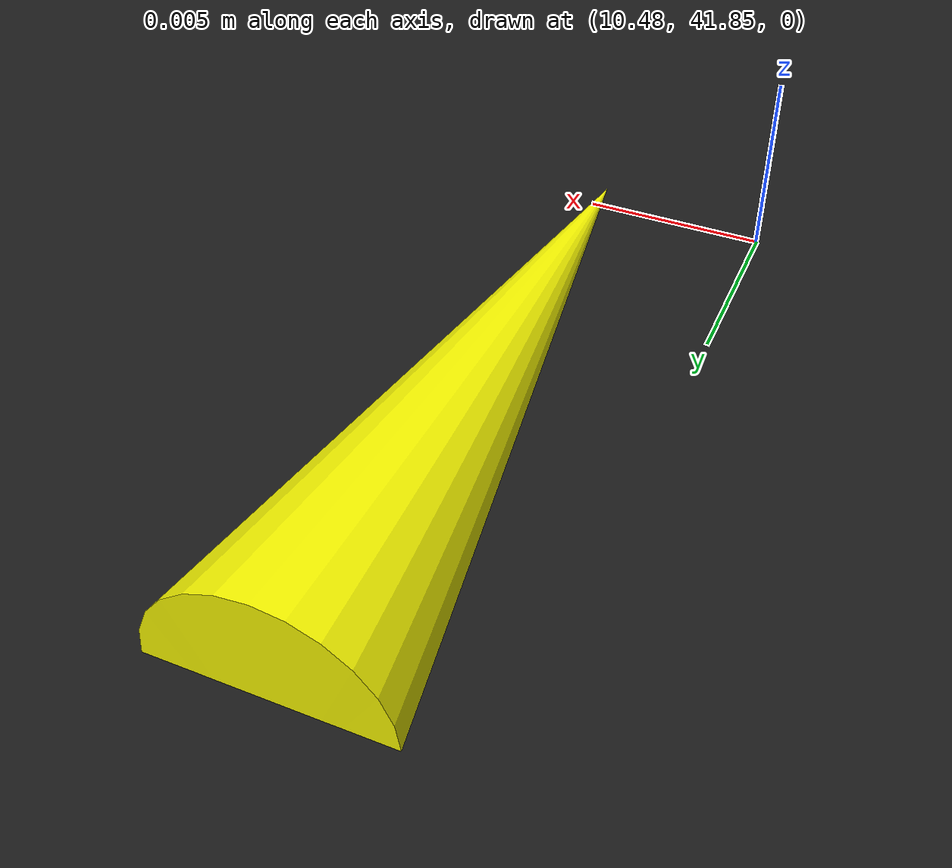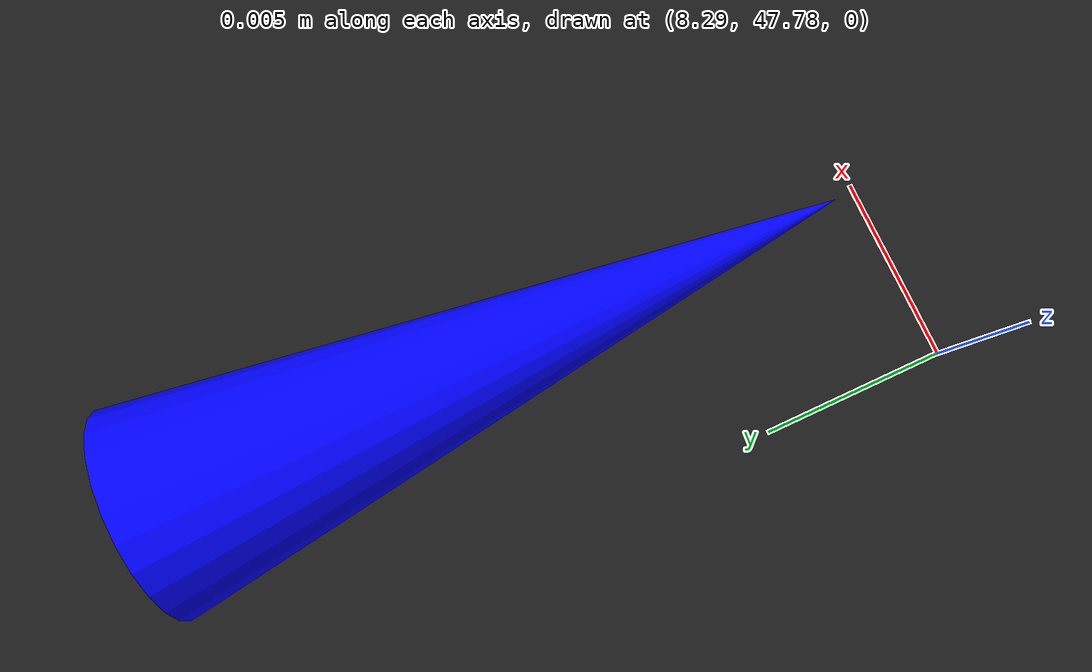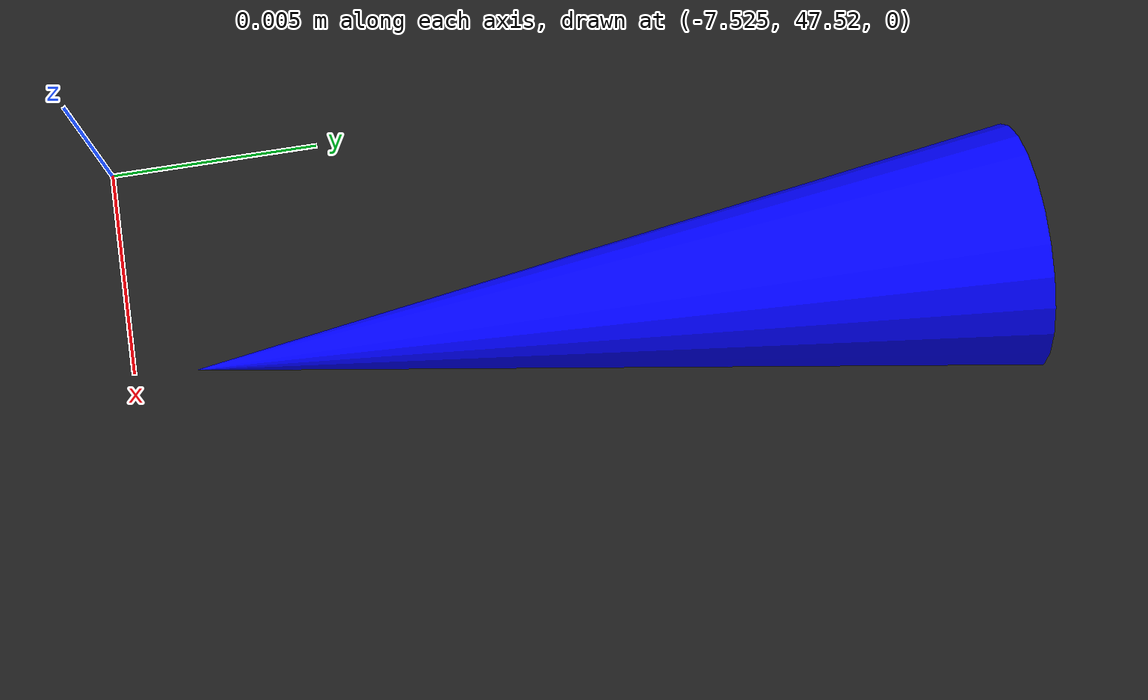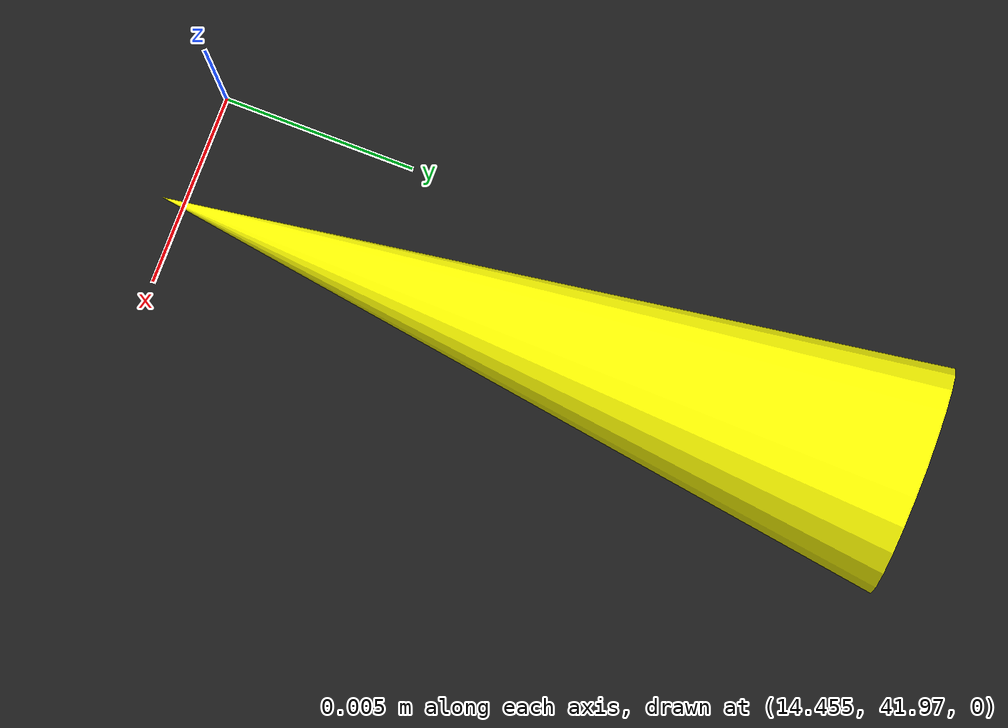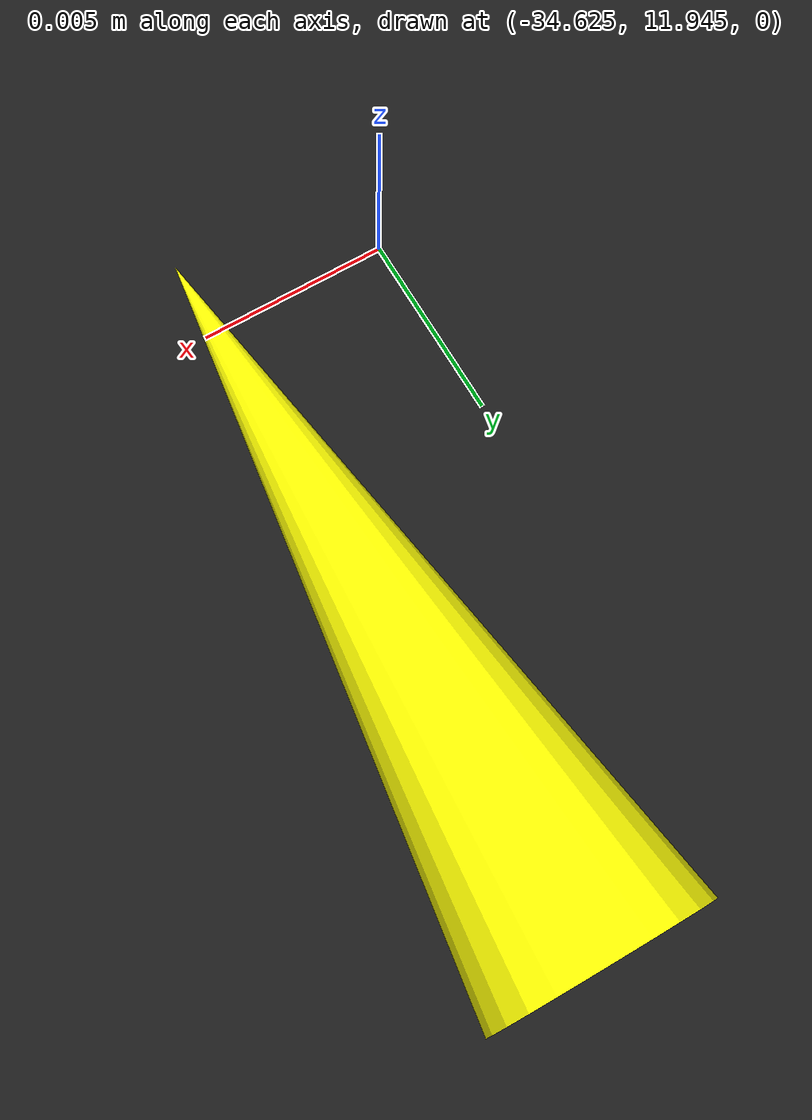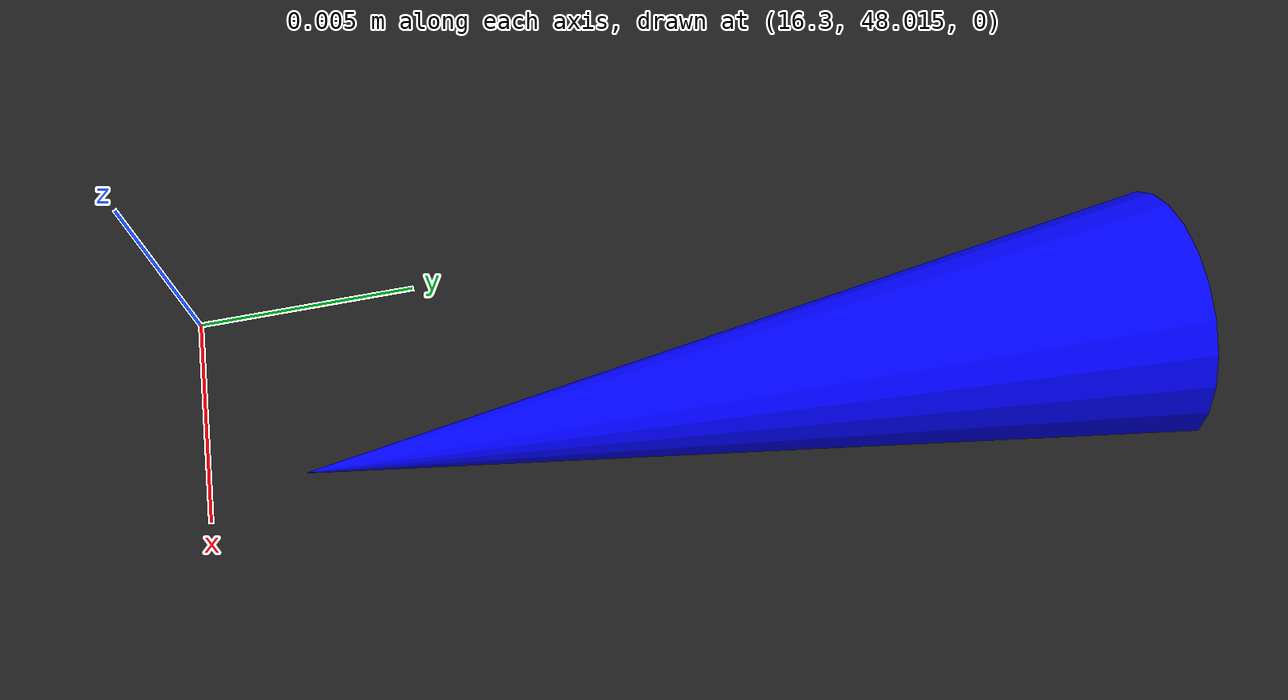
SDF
<?xml version="1.0"?>
<sdf version="1.9">
	<world name="track">
		<!-- PHYSICS -->
		<physics name="1ms" type="ignored">
			<max_step_size>
				0.001
			</max_step_size>
			<real_time_factor>
				1.0
			</real_time_factor>
		</physics>
		<gravity>
			0 0 -9.8
		</gravity>
		<magnetic_field>
			6e-06 2.3e-05 -4.2e-05
		</magnetic_field>
		<atmosphere type="adiabatic" />
		<!-- PLUGINS -->
		<plugin name="gz::sim::systems::Physics" filename="gz-sim-physics-system" />
		<plugin name="gz::sim::systems::UserCommands" filename="gz-sim-user-commands-system" />
		<plugin name="gz::sim::systems::SceneBroadcaster" filename="gz-sim-scene-broadcaster-system" />
		<gui fullscreen="0">
			<!-- 3D scene -->
			<plugin filename="MinimalScene" name="3D View">
				<gz-gui>
					<title>
						3D View
					</title>
					<property type="bool" key="showTitleBar">
						false
					</property>
					<property type="string" key="state">
						docked
					</property>
				</gz-gui>
				<engine>
					ogre2
				</engine>
				<scene>
					scene
				</scene>
				<ambient_light>
					0.4 0.4 0.4
				</ambient_light>
				<background_color>
					0.8 0.8 0.8
				</background_color>
				<camera_pose>
					-6 0 6 0 0.5 0
				</camera_pose>
			</plugin>
			<!-- Plugins that add functionality to the scene -->
			<plugin filename="EntityContextMenuPlugin" name="Entity context menu">
				<gz-gui>
					<property key="state" type="string">
						floating
					</property>
					<property key="width" type="double">
						5
					</property>
					<property key="height" type="double">
						5
					</property>
					<property key="showTitleBar" type="bool">
						false
					</property>
				</gz-gui>
			</plugin>
			<plugin filename="GzSceneManager" name="Scene Manager">
				<gz-gui>
					<property key="resizable" type="bool">
						false
					</property>
					<property key="width" type="double">
						5
					</property>
					<property key="height" type="double">
						5
					</property>
					<property key="state" type="string">
						floating
					</property>
					<property key="showTitleBar" type="bool">
						false
					</property>
				</gz-gui>
			</plugin>
			<plugin filename="InteractiveViewControl" name="Interactive view control">
				<gz-gui>
					<property key="resizable" type="bool">
						false
					</property>
					<property key="width" type="double">
						5
					</property>
					<property key="height" type="double">
						5
					</property>
					<property key="state" type="string">
						floating
					</property>
					<property key="showTitleBar" type="bool">
						false
					</property>
				</gz-gui>
			</plugin>
			<plugin filename="CameraTracking" name="Camera Tracking">
				<gz-gui>
					<property key="resizable" type="bool">
						false
					</property>
					<property key="width" type="double">
						5
					</property>
					<property key="height" type="double">
						5
					</property>
					<property key="state" type="string">
						floating
					</property>
					<property key="showTitleBar" type="bool">
						false
					</property>
				</gz-gui>
			</plugin>
			<plugin name="World control" filename="WorldControl">
				<gz-gui>
					<title>
						World control
					</title>
					<property type="bool" key="showTitleBar">
						0
					</property>
					<property type="bool" key="resizable">
						0
					</property>
					<property type="double" key="height">
						72
					</property>
					<property type="double" key="z">
						1
					</property>
					<property type="string" key="state">
						floating
					</property>
					<anchors target="3D View">
						<line own="left" target="left" />
						<line own="bottom" target="bottom" />
					</anchors>
				</gz-gui>
				<play_pause>
					1
				</play_pause>
				<step>
					1
				</step>
				<start_paused>
					1
				</start_paused>
			</plugin>
			<plugin name="World stats" filename="WorldStats">
				<gz-gui>
					<title>
						World stats
					</title>
					<property type="bool" key="showTitleBar">
						0
					</property>
					<property type="bool" key="resizable">
						0
					</property>
					<property type="double" key="height">
						110
					</property>
					<property type="double" key="width">
						290
					</property>
					<property type="double" key="z">
						1
					</property>
					<property type="string" key="state">
						floating
					</property>
					<anchors target="3D View">
						<line own="right" target="right" />
						<line own="bottom" target="bottom" />
					</anchors>
				</gz-gui>
				<sim_time>
					1
				</sim_time>
				<real_time>
					1
				</real_time>
				<real_time_factor>
					1
				</real_time_factor>
				<iterations>
					1
				</iterations>
			</plugin>
			<plugin filename="VisualizeLidar" name="Visualize Lidar">
			</plugin>
			<plugin filename="ImageDisplay" name="Image Display">
			</plugin>
			<!-- Inspector -->
			<plugin filename="ComponentInspector" name="Component inspector">
				<ignition-gui>
					<property type="string" key="state">
						docked
					</property>
				</ignition-gui>
			</plugin>
			<!-- Entity tree -->
			<plugin filename="EntityTree" name="Entity tree">
				<ignition-gui>
					<property type="string" key="state">
						docked
					</property>
				</ignition-gui>
			</plugin>
		</gui>
		<!-- SENSORS -->
		<plugin filename="gz-sim-sensors-system" name="gz::sim::systems::Sensors">
			<render_engine>
				ogre2
			</render_engine>
		</plugin>
		<!-- AMBIENT -->
		<scene>
			<ambient>
				1 1 1 1
			</ambient>
			<background>
				0.8 0.8 0.8 1
			</background>
			<shadows>
				1
			</shadows>
		</scene>
		<light name="sun" type="directional">
			<cast_shadows>
				1
			</cast_shadows>
			<pose>
				0 0 10 0 0 0
			</pose>
			<diffuse>
				0.8 0.8 0.8 1
			</diffuse>
			<specular>
				0.8 0.8 0.8 1
			</specular>
			<attenuation>
				<range>
					1000
				</range>
				<constant>
					0.9
				</constant>
				<linear>
					0.01
				</linear>
				<quadratic>
					0.001
				</quadratic>
			</attenuation>
			<direction>
				-0.5 0.1 -0.9
			</direction>
		</light>
		<model name="ground_plane">
			<static>
				true
			</static>
			<link name="link">
				<collision name="collision">
					<geometry>
						<plane>
							<normal>
								0 0 1
							</normal>
							<size>
								100 100
							</size>
						</plane>
					</geometry>
					<surface>
						<friction>
							<dart />
						</friction>
						<bounce />
						<contact />
					</surface>
				</collision>
				<visual name="visual">
					<geometry>
						<plane>
							<normal>
								0 0 1
							</normal>
							<size>
								100 100
							</size>
						</plane>
					</geometry>
					<material>
						<ambient>
							0.1 0.1 0.1 1
						</ambient>
						<diffuse>
							0.1 0.1 0.1 1
						</diffuse>
						<specular>
							0.8 0.8 0.8 1
						</specular>
					</material>
				</visual>
				<pose>
					0 0 0 0 -0 0
				</pose>
				<inertial>
					<pose>
						0 0 0 0 -0 0
					</pose>
					<mass>
						1
					</mass>
					<inertia>
						<ixx>
							1
						</ixx>
						<ixy>
							0
						</ixy>
						<ixz>
							0
						</ixz>
						<iyy>
							1
						</iyy>
						<iyz>
							0
						</iyz>
						<izz>
							1
						</izz>
					</inertia>
				</inertial>
				<enable_wind>
					false
				</enable_wind>
			</link>
			<pose>
				0 0 0 0 -0 0
			</pose>
			<self_collide>
				false
			</self_collide>
		</model>
		<!-- TRACK -->
		<model name="cones">
			<pose>
				0 0 0 0 0 0
			</pose>
			<link name="cone_0_link">
				<collision name="cone_0_collision">
					<geometry>
						<mesh>
							<uri>
								/home/ubuntu/psd_ws/src/psd_gazebo_sim/psd_gazebo_worlds/world/models/cone/meshes/cone.stl
							</uri>
							<scale>
								0.001 0.001 0.001
							</scale>
						</mesh>
					</geometry>
				</collision>
				<visual name="cone_0_visual">
					<geometry>
						<mesh>
							<uri>
								/home/ubuntu/psd_ws/src/psd_gazebo_sim/psd_gazebo_worlds/world/models/cone/meshes/cone.stl
							</uri>
							<scale>
								0.001 0.001 0.001
							</scale>
						</mesh>
					</geometry>
					<material>
						<ambient>
							1 1 0 1
						</ambient>
						<diffuse>
							1 1 0 1
						</diffuse>
						<specular>
							1 1 0 1
						</specular>
					</material>
				</visual>
				<pose>
					6.49447171658257 41.7389113024907 0.0 1.57 0 0
				</pose>
				<enable_wind>
					false
				</enable_wind>
			</link>
			<link name="cone_1_link">
				<collision name="cone_1_collision">
					<geometry>
						<mesh>
							<uri>
								/home/ubuntu/psd_ws/src/psd_gazebo_sim/psd_gazebo_worlds/world/models/cone/meshes/cone.stl
							</uri>
							<scale>
								0.001 0.001 0.001
							</scale>
						</mesh>
					</geometry>
				</collision>
				<visual name="cone_1_visual">
					<geometry>
						<mesh>
							<uri>
								/home/ubuntu/psd_ws/src/psd_gazebo_sim/psd_gazebo_worlds/world/models/cone/meshes/cone.stl
							</uri>
							<scale>
								0.001 0.001 0.001
							</scale>
						</mesh>
					</geometry>
					<material>
						<ambient>
							1 1 0 1
						</ambient>
						<diffuse>
							1 1 0 1
						</diffuse>
						<specular>
							1 1 0 1
						</specular>
					</material>
				</visual>
				<pose>
					10.4848751821667 41.8690573815958 0.0 1.57 0 0
				</pose>
				<enable_wind>
					false
				</enable_wind>
			</link>
			<link name="cone_2_link">
				<collision name="cone_2_collision">
					<geometry>
						<mesh>
							<uri>
								/home/ubuntu/psd_ws/src/psd_gazebo_sim/psd_gazebo_worlds/world/models/cone/meshes/cone.stl
							</uri>
							<scale>
								0.001 0.001 0.001
							</scale>
						</mesh>
					</geometry>
				</collision>
				<visual name="cone_2_visual">
					<geometry>
						<mesh>
							<uri>
								/home/ubuntu/psd_ws/src/psd_gazebo_sim/psd_gazebo_worlds/world/models/cone/meshes/cone.stl
							</uri>
							<scale>
								0.001 0.001 0.001
							</scale>
						</mesh>
					</geometry>
					<material>
						<ambient>
							1 1 0 1
						</ambient>
						<diffuse>
							1 1 0 1
						</diffuse>
						<specular>
							1 1 0 1
						</specular>
					</material>
				</visual>
				<pose>
					14.4579005366844 41.9894100214277 0.0 1.57 0 0
				</pose>
				<enable_wind>
					false
				</enable_wind>
			</link>
			<link name="cone_3_link">
				<collision name="cone_3_collision">
					<geometry>
						<mesh>
							<uri>
								/home/ubuntu/psd_ws/src/psd_gazebo_sim/psd_gazebo_worlds/world/models/cone/meshes/cone.stl
							</uri>
							<scale>
								0.001 0.001 0.001
							</scale>
						</mesh>
					</geometry>
				</collision>
				<visual name="cone_3_visual">
					<geometry>
						<mesh>
							<uri>
								/home/ubuntu/psd_ws/src/psd_gazebo_sim/psd_gazebo_worlds/world/models/cone/meshes/cone.stl
							</uri>
							<scale>
								0.001 0.001 0.001
							</scale>
						</mesh>
					</geometry>
					<material>
						<ambient>
							1 1 0 1
						</ambient>
						<diffuse>
							1 1 0 1
						</diffuse>
						<specular>
							1 1 0 1
						</specular>
					</material>
				</visual>
				<pose>
					22.3534294484539 42.1081444836209 0.0 1.57 0 0
				</pose>
				<enable_wind>
					false
				</enable_wind>
			</link>
			<link name="cone_4_link">
				<collision name="cone_4_collision">
					<geometry>
						<mesh>
							<uri>
								/home/ubuntu/psd_ws/src/psd_gazebo_sim/psd_gazebo_worlds/world/models/cone/meshes/cone.stl
							</uri>
							<scale>
								0.001 0.001 0.001
							</scale>
						</mesh>
					</geometry>
				</collision>
				<visual name="cone_4_visual">
					<geometry>
						<mesh>
							<uri>
								/home/ubuntu/psd_ws/src/psd_gazebo_sim/psd_gazebo_worlds/world/models/cone/meshes/cone.stl
							</uri>
							<scale>
								0.001 0.001 0.001
							</scale>
						</mesh>
					</geometry>
					<material>
						<ambient>
							1 1 0 1
						</ambient>
						<diffuse>
							1 1 0 1
						</diffuse>
						<specular>
							1 1 0 1
						</specular>
					</material>
				</visual>
				<pose>
					26.2748937812757 42.0609961552005 0.0 1.57 0 0
				</pose>
				<enable_wind>
					false
				</enable_wind>
			</link>
			<link name="cone_5_link">
				<collision name="cone_5_collision">
					<geometry>
						<mesh>
							<uri>
								/home/ubuntu/psd_ws/src/psd_gazebo_sim/psd_gazebo_worlds/world/models/cone/meshes/cone.stl
							</uri>
							<scale>
								0.001 0.001 0.001
							</scale>
						</mesh>
					</geometry>
				</collision>
				<visual name="cone_5_visual">
					<geometry>
						<mesh>
							<uri>
								/home/ubuntu/psd_ws/src/psd_gazebo_sim/psd_gazebo_worlds/world/models/cone/meshes/cone.stl
							</uri>
							<scale>
								0.001 0.001 0.001
							</scale>
						</mesh>
					</geometry>
					<material>
						<ambient>
							1 1 0 1
						</ambient>
						<diffuse>
							1 1 0 1
						</diffuse>
						<specular>
							1 1 0 1
						</specular>
					</material>
				</visual>
				<pose>
					30.1761149294924 41.9130441723441 0.0 1.57 0 0
				</pose>
				<enable_wind>
					false
				</enable_wind>
			</link>
			<link name="cone_6_link">
				<collision name="cone_6_collision">
					<geometry>
						<mesh>
							<uri>
								/home/ubuntu/psd_ws/src/psd_gazebo_sim/psd_gazebo_worlds/world/models/cone/meshes/cone.stl
							</uri>
							<scale>
								0.001 0.001 0.001
							</scale>
						</mesh>
					</geometry>
				</collision>
				<visual name="cone_6_visual">
					<geometry>
						<mesh>
							<uri>
								/home/ubuntu/psd_ws/src/psd_gazebo_sim/psd_gazebo_worlds/world/models/cone/meshes/cone.stl
							</uri>
							<scale>
								0.001 0.001 0.001
							</scale>
						</mesh>
					</geometry>
					<material>
						<ambient>
							1 1 0 1
						</ambient>
						<diffuse>
							1 1 0 1
						</diffuse>
						<specular>
							1 1 0 1
						</specular>
					</material>
				</visual>
				<pose>
					33.88171993278 41.5914171121172 0.0 1.57 0 0
				</pose>
				<enable_wind>
					false
				</enable_wind>
			</link>
			<link name="cone_7_link">
				<collision name="cone_7_collision">
					<geometry>
						<mesh>
							<uri>
								/home/ubuntu/psd_ws/src/psd_gazebo_sim/psd_gazebo_worlds/world/models/cone/meshes/cone.stl
							</uri>
							<scale>
								0.001 0.001 0.001
							</scale>
						</mesh>
					</geometry>
				</collision>
				<visual name="cone_7_visual">
					<geometry>
						<mesh>
							<uri>
								/home/ubuntu/psd_ws/src/psd_gazebo_sim/psd_gazebo_worlds/world/models/cone/meshes/cone.stl
							</uri>
							<scale>
								0.001 0.001 0.001
							</scale>
						</mesh>
					</geometry>
					<material>
						<ambient>
							1 1 0 1
						</ambient>
						<diffuse>
							1 1 0 1
						</diffuse>
						<specular>
							1 1 0 1
						</specular>
					</material>
				</visual>
				<pose>
					38.5108000329817 40.1631834270328 0.0 1.57 0 0
				</pose>
				<enable_wind>
					false
				</enable_wind>
			</link>
			<link name="cone_8_link">
				<collision name="cone_8_collision">
					<geometry>
						<mesh>
							<uri>
								/home/ubuntu/psd_ws/src/psd_gazebo_sim/psd_gazebo_worlds/world/models/cone/meshes/cone.stl
							</uri>
							<scale>
								0.001 0.001 0.001
							</scale>
						</mesh>
					</geometry>
				</collision>
				<visual name="cone_8_visual">
					<geometry>
						<mesh>
							<uri>
								/home/ubuntu/psd_ws/src/psd_gazebo_sim/psd_gazebo_worlds/world/models/cone/meshes/cone.stl
							</uri>
							<scale>
								0.001 0.001 0.001
							</scale>
						</mesh>
					</geometry>
					<material>
						<ambient>
							1 1 0 1
						</ambient>
						<diffuse>
							1 1 0 1
						</diffuse>
						<specular>
							1 1 0 1
						</specular>
					</material>
				</visual>
				<pose>
					41.6428012725483 37.057274095852 0.0 1.57 0 0
				</pose>
				<enable_wind>
					false
				</enable_wind>
			</link>
			<link name="cone_9_link">
				<collision name="cone_9_collision">
					<geometry>
						<mesh>
							<uri>
								/home/ubuntu/psd_ws/src/psd_gazebo_sim/psd_gazebo_worlds/world/models/cone/meshes/cone.stl
							</uri>
							<scale>
								0.001 0.001 0.001
							</scale>
						</mesh>
					</geometry>
				</collision>
				<visual name="cone_9_visual">
					<geometry>
						<mesh>
							<uri>
								/home/ubuntu/psd_ws/src/psd_gazebo_sim/psd_gazebo_worlds/world/models/cone/meshes/cone.stl
							</uri>
							<scale>
								0.001 0.001 0.001
							</scale>
						</mesh>
					</geometry>
					<material>
						<ambient>
							1 1 0 1
						</ambient>
						<diffuse>
							1 1 0 1
						</diffuse>
						<specular>
							1 1 0 1
						</specular>
					</material>
				</visual>
				<pose>
					42.923741279885 34.1220862330776 0.0 1.57 0 0
				</pose>
				<enable_wind>
					false
				</enable_wind>
			</link>
			<link name="cone_10_link">
				<collision name="cone_10_collision">
					<geometry>
						<mesh>
							<uri>
								/home/ubuntu/psd_ws/src/psd_gazebo_sim/psd_gazebo_worlds/world/models/cone/meshes/cone.stl
							</uri>
							<scale>
								0.001 0.001 0.001
							</scale>
						</mesh>
					</geometry>
				</collision>
				<visual name="cone_10_visual">
					<geometry>
						<mesh>
							<uri>
								/home/ubuntu/psd_ws/src/psd_gazebo_sim/psd_gazebo_worlds/world/models/cone/meshes/cone.stl
							</uri>
							<scale>
								0.001 0.001 0.001
							</scale>
						</mesh>
					</geometry>
					<material>
						<ambient>
							1 1 0 1
						</ambient>
						<diffuse>
							1 1 0 1
						</diffuse>
						<specular>
							1 1 0 1
						</specular>
					</material>
				</visual>
				<pose>
					43.4041825643156 29.3682424552239 0.0 1.57 0 0
				</pose>
				<enable_wind>
					false
				</enable_wind>
			</link>
			<link name="cone_11_link">
				<collision name="cone_11_collision">
					<geometry>
						<mesh>
							<uri>
								/home/ubuntu/psd_ws/src/psd_gazebo_sim/psd_gazebo_worlds/world/models/cone/meshes/cone.stl
							</uri>
							<scale>
								0.001 0.001 0.001
							</scale>
						</mesh>
					</geometry>
				</collision>
				<visual name="cone_11_visual">
					<geometry>
						<mesh>
							<uri>
								/home/ubuntu/psd_ws/src/psd_gazebo_sim/psd_gazebo_worlds/world/models/cone/meshes/cone.stl
							</uri>
							<scale>
								0.001 0.001 0.001
							</scale>
						</mesh>
					</geometry>
					<material>
						<ambient>
							1 1 0 1
						</ambient>
						<diffuse>
							1 1 0 1
						</diffuse>
						<specular>
							1 1 0 1
						</specular>
					</material>
				</visual>
				<pose>
					42.6373380962399 26.4081334491868 0.0 1.57 0 0
				</pose>
				<enable_wind>
					false
				</enable_wind>
			</link>
			<link name="cone_12_link">
				<collision name="cone_12_collision">
					<geometry>
						<mesh>
							<uri>
								/home/ubuntu/psd_ws/src/psd_gazebo_sim/psd_gazebo_worlds/world/models/cone/meshes/cone.stl
							</uri>
							<scale>
								0.001 0.001 0.001
							</scale>
						</mesh>
					</geometry>
				</collision>
				<visual name="cone_12_visual">
					<geometry>
						<mesh>
							<uri>
								/home/ubuntu/psd_ws/src/psd_gazebo_sim/psd_gazebo_worlds/world/models/cone/meshes/cone.stl
							</uri>
							<scale>
								0.001 0.001 0.001
							</scale>
						</mesh>
					</geometry>
					<material>
						<ambient>
							1 1 0 1
						</ambient>
						<diffuse>
							1 1 0 1
						</diffuse>
						<specular>
							1 1 0 1
						</specular>
					</material>
				</visual>
				<pose>
					39.8493389129556 22.6733478226331 0.0 1.57 0 0
				</pose>
				<enable_wind>
					false
				</enable_wind>
			</link>
			<link name="cone_13_link">
				<collision name="cone_13_collision">
					<geometry>
						<mesh>
							<uri>
								/home/ubuntu/psd_ws/src/psd_gazebo_sim/psd_gazebo_worlds/world/models/cone/meshes/cone.stl
							</uri>
							<scale>
								0.001 0.001 0.001
							</scale>
						</mesh>
					</geometry>
				</collision>
				<visual name="cone_13_visual">
					<geometry>
						<mesh>
							<uri>
								/home/ubuntu/psd_ws/src/psd_gazebo_sim/psd_gazebo_worlds/world/models/cone/meshes/cone.stl
							</uri>
							<scale>
								0.001 0.001 0.001
							</scale>
						</mesh>
					</geometry>
					<material>
						<ambient>
							1 1 0 1
						</ambient>
						<diffuse>
							1 1 0 1
						</diffuse>
						<specular>
							1 1 0 1
						</specular>
					</material>
				</visual>
				<pose>
					35.6438750732877 19.9947555768891 0.0 1.57 0 0
				</pose>
				<enable_wind>
					false
				</enable_wind>
			</link>
			<link name="cone_14_link">
				<collision name="cone_14_collision">
					<geometry>
						<mesh>
							<uri>
								/home/ubuntu/psd_ws/src/psd_gazebo_sim/psd_gazebo_worlds/world/models/cone/meshes/cone.stl
							</uri>
							<scale>
								0.001 0.001 0.001
							</scale>
						</mesh>
					</geometry>
				</collision>
				<visual name="cone_14_visual">
					<geometry>
						<mesh>
							<uri>
								/home/ubuntu/psd_ws/src/psd_gazebo_sim/psd_gazebo_worlds/world/models/cone/meshes/cone.stl
							</uri>
							<scale>
								0.001 0.001 0.001
							</scale>
						</mesh>
					</geometry>
					<material>
						<ambient>
							1 1 0 1
						</ambient>
						<diffuse>
							1 1 0 1
						</diffuse>
						<specular>
							1 1 0 1
						</specular>
					</material>
				</visual>
				<pose>
					32.5117013027651 19.0709696852617 0.0 1.57 0 0
				</pose>
				<enable_wind>
					false
				</enable_wind>
			</link>
			<link name="cone_15_link">
				<collision name="cone_15_collision">
					<geometry>
						<mesh>
							<uri>
								/home/ubuntu/psd_ws/src/psd_gazebo_sim/psd_gazebo_worlds/world/models/cone/meshes/cone.stl
							</uri>
							<scale>
								0.001 0.001 0.001
							</scale>
						</mesh>
					</geometry>
				</collision>
				<visual name="cone_15_visual">
					<geometry>
						<mesh>
							<uri>
								/home/ubuntu/psd_ws/src/psd_gazebo_sim/psd_gazebo_worlds/world/models/cone/meshes/cone.stl
							</uri>
							<scale>
								0.001 0.001 0.001
							</scale>
						</mesh>
					</geometry>
					<material>
						<ambient>
							1 1 0 1
						</ambient>
						<diffuse>
							1 1 0 1
						</diffuse>
						<specular>
							1 1 0 1
						</specular>
					</material>
				</visual>
				<pose>
					29.305019764528 18.9545691109581 0.0 1.57 0 0
				</pose>
				<enable_wind>
					false
				</enable_wind>
			</link>
			<link name="cone_16_link">
				<collision name="cone_16_collision">
					<geometry>
						<mesh>
							<uri>
								/home/ubuntu/psd_ws/src/psd_gazebo_sim/psd_gazebo_worlds/world/models/cone/meshes/cone.stl
							</uri>
							<scale>
								0.001 0.001 0.001
							</scale>
						</mesh>
					</geometry>
				</collision>
				<visual name="cone_16_visual">
					<geometry>
						<mesh>
							<uri>
								/home/ubuntu/psd_ws/src/psd_gazebo_sim/psd_gazebo_worlds/world/models/cone/meshes/cone.stl
							</uri>
							<scale>
								0.001 0.001 0.001
							</scale>
						</mesh>
					</geometry>
					<material>
						<ambient>
							1 1 0 1
						</ambient>
						<diffuse>
							1 1 0 1
						</diffuse>
						<specular>
							1 1 0 1
						</specular>
					</material>
				</visual>
				<pose>
					24.4759113345748 20.2570787967781 0.0 1.57 0 0
				</pose>
				<enable_wind>
					false
				</enable_wind>
			</link>
			<link name="cone_17_link">
				<collision name="cone_17_collision">
					<geometry>
						<mesh>
							<uri>
								/home/ubuntu/psd_ws/src/psd_gazebo_sim/psd_gazebo_worlds/world/models/cone/meshes/cone.stl
							</uri>
							<scale>
								0.001 0.001 0.001
							</scale>
						</mesh>
					</geometry>
				</collision>
				<visual name="cone_17_visual">
					<geometry>
						<mesh>
							<uri>
								/home/ubuntu/psd_ws/src/psd_gazebo_sim/psd_gazebo_worlds/world/models/cone/meshes/cone.stl
							</uri>
							<scale>
								0.001 0.001 0.001
							</scale>
						</mesh>
					</geometry>
					<material>
						<ambient>
							1 1 0 1
						</ambient>
						<diffuse>
							1 1 0 1
						</diffuse>
						<specular>
							1 1 0 1
						</specular>
					</material>
				</visual>
				<pose>
					19.8072187451783 22.9775182612717 0.0 1.57 0 0
				</pose>
				<enable_wind>
					false
				</enable_wind>
			</link>
			<link name="cone_18_link">
				<collision name="cone_18_collision">
					<geometry>
						<mesh>
							<uri>
								/home/ubuntu/psd_ws/src/psd_gazebo_sim/psd_gazebo_worlds/world/models/cone/meshes/cone.stl
							</uri>
							<scale>
								0.001 0.001 0.001
							</scale>
						</mesh>
					</geometry>
				</collision>
				<visual name="cone_18_visual">
					<geometry>
						<mesh>
							<uri>
								/home/ubuntu/psd_ws/src/psd_gazebo_sim/psd_gazebo_worlds/world/models/cone/meshes/cone.stl
							</uri>
							<scale>
								0.001 0.001 0.001
							</scale>
						</mesh>
					</geometry>
					<material>
						<ambient>
							1 1 0 1
						</ambient>
						<diffuse>
							1 1 0 1
						</diffuse>
						<specular>
							1 1 0 1
						</specular>
					</material>
				</visual>
				<pose>
					16.5291821840059 25.277806927272 0.0 1.57 0 0
				</pose>
				<enable_wind>
					false
				</enable_wind>
			</link>
			<link name="cone_19_link">
				<collision name="cone_19_collision">
					<geometry>
						<mesh>
							<uri>
								/home/ubuntu/psd_ws/src/psd_gazebo_sim/psd_gazebo_worlds/world/models/cone/meshes/cone.stl
							</uri>
							<scale>
								0.001 0.001 0.001
							</scale>
						</mesh>
					</geometry>
				</collision>
				<visual name="cone_19_visual">
					<geometry>
						<mesh>
							<uri>
								/home/ubuntu/psd_ws/src/psd_gazebo_sim/psd_gazebo_worlds/world/models/cone/meshes/cone.stl
							</uri>
							<scale>
								0.001 0.001 0.001
							</scale>
						</mesh>
					</geometry>
					<material>
						<ambient>
							1 1 0 1
						</ambient>
						<diffuse>
							1 1 0 1
						</diffuse>
						<specular>
							1 1 0 1
						</specular>
					</material>
				</visual>
				<pose>
					10.7566166245341 28.5122919557571 0.0 1.57 0 0
				</pose>
				<enable_wind>
					false
				</enable_wind>
			</link>
			<link name="cone_20_link">
				<collision name="cone_20_collision">
					<geometry>
						<mesh>
							<uri>
								/home/ubuntu/psd_ws/src/psd_gazebo_sim/psd_gazebo_worlds/world/models/cone/meshes/cone.stl
							</uri>
							<scale>
								0.001 0.001 0.001
							</scale>
						</mesh>
					</geometry>
				</collision>
				<visual name="cone_20_visual">
					<geometry>
						<mesh>
							<uri>
								/home/ubuntu/psd_ws/src/psd_gazebo_sim/psd_gazebo_worlds/world/models/cone/meshes/cone.stl
							</uri>
							<scale>
								0.001 0.001 0.001
							</scale>
						</mesh>
					</geometry>
					<material>
						<ambient>
							1 1 0 1
						</ambient>
						<diffuse>
							1 1 0 1
						</diffuse>
						<specular>
							1 1 0 1
						</specular>
					</material>
				</visual>
				<pose>
					6.36970146209175 29.8034933598624 0.0 1.57 0 0
				</pose>
				<enable_wind>
					false
				</enable_wind>
			</link>
			<link name="cone_21_link">
				<collision name="cone_21_collision">
					<geometry>
						<mesh>
							<uri>
								/home/ubuntu/psd_ws/src/psd_gazebo_sim/psd_gazebo_worlds/world/models/cone/meshes/cone.stl
							</uri>
							<scale>
								0.001 0.001 0.001
							</scale>
						</mesh>
					</geometry>
				</collision>
				<visual name="cone_21_visual">
					<geometry>
						<mesh>
							<uri>
								/home/ubuntu/psd_ws/src/psd_gazebo_sim/psd_gazebo_worlds/world/models/cone/meshes/cone.stl
							</uri>
							<scale>
								0.001 0.001 0.001
							</scale>
						</mesh>
					</geometry>
					<material>
						<ambient>
							1 1 0 1
						</ambient>
						<diffuse>
							1 1 0 1
						</diffuse>
						<specular>
							1 1 0 1
						</specular>
					</material>
				</visual>
				<pose>
					-0.405973075502234 30.1500578730274 0.0 1.57 0 0
				</pose>
				<enable_wind>
					false
				</enable_wind>
			</link>
			<link name="cone_22_link">
				<collision name="cone_22_collision">
					<geometry>
						<mesh>
							<uri>
								/home/ubuntu/psd_ws/src/psd_gazebo_sim/psd_gazebo_worlds/world/models/cone/meshes/cone.stl
							</uri>
							<scale>
								0.001 0.001 0.001
							</scale>
						</mesh>
					</geometry>
				</collision>
				<visual name="cone_22_visual">
					<geometry>
						<mesh>
							<uri>
								/home/ubuntu/psd_ws/src/psd_gazebo_sim/psd_gazebo_worlds/world/models/cone/meshes/cone.stl
							</uri>
							<scale>
								0.001 0.001 0.001
							</scale>
						</mesh>
					</geometry>
					<material>
						<ambient>
							1 1 0 1
						</ambient>
						<diffuse>
							1 1 0 1
						</diffuse>
						<specular>
							1 1 0 1
						</specular>
					</material>
				</visual>
				<pose>
					-7.53032772904185 27.7630095130657 0.0 1.57 0 0
				</pose>
				<enable_wind>
					false
				</enable_wind>
			</link>
			<link name="cone_23_link">
				<collision name="cone_23_collision">
					<geometry>
						<mesh>
							<uri>
								/home/ubuntu/psd_ws/src/psd_gazebo_sim/psd_gazebo_worlds/world/models/cone/meshes/cone.stl
							</uri>
							<scale>
								0.001 0.001 0.001
							</scale>
						</mesh>
					</geometry>
				</collision>
				<visual name="cone_23_visual">
					<geometry>
						<mesh>
							<uri>
								/home/ubuntu/psd_ws/src/psd_gazebo_sim/psd_gazebo_worlds/world/models/cone/meshes/cone.stl
							</uri>
							<scale>
								0.001 0.001 0.001
							</scale>
						</mesh>
					</geometry>
					<material>
						<ambient>
							1 1 0 1
						</ambient>
						<diffuse>
							1 1 0 1
						</diffuse>
						<specular>
							1 1 0 1
						</specular>
					</material>
				</visual>
				<pose>
					-10.9967405848897 23.4446538263345 0.0 1.57 0 0
				</pose>
				<enable_wind>
					false
				</enable_wind>
			</link>
			<link name="cone_24_link">
				<collision name="cone_24_collision">
					<geometry>
						<mesh>
							<uri>
								/home/ubuntu/psd_ws/src/psd_gazebo_sim/psd_gazebo_worlds/world/models/cone/meshes/cone.stl
							</uri>
							<scale>
								0.001 0.001 0.001
							</scale>
						</mesh>
					</geometry>
				</collision>
				<visual name="cone_24_visual">
					<geometry>
						<mesh>
							<uri>
								/home/ubuntu/psd_ws/src/psd_gazebo_sim/psd_gazebo_worlds/world/models/cone/meshes/cone.stl
							</uri>
							<scale>
								0.001 0.001 0.001
							</scale>
						</mesh>
					</geometry>
					<material>
						<ambient>
							1 1 0 1
						</ambient>
						<diffuse>
							1 1 0 1
						</diffuse>
						<specular>
							1 1 0 1
						</specular>
					</material>
				</visual>
				<pose>
					-11.7945553145768 18.0098876247875 0.0 1.57 0 0
				</pose>
				<enable_wind>
					false
				</enable_wind>
			</link>
			<link name="cone_25_link">
				<collision name="cone_25_collision">
					<geometry>
						<mesh>
							<uri>
								/home/ubuntu/psd_ws/src/psd_gazebo_sim/psd_gazebo_worlds/world/models/cone/meshes/cone.stl
							</uri>
							<scale>
								0.001 0.001 0.001
							</scale>
						</mesh>
					</geometry>
				</collision>
				<visual name="cone_25_visual">
					<geometry>
						<mesh>
							<uri>
								/home/ubuntu/psd_ws/src/psd_gazebo_sim/psd_gazebo_worlds/world/models/cone/meshes/cone.stl
							</uri>
							<scale>
								0.001 0.001 0.001
							</scale>
						</mesh>
					</geometry>
					<material>
						<ambient>
							1 1 0 1
						</ambient>
						<diffuse>
							1 1 0 1
						</diffuse>
						<specular>
							1 1 0 1
						</specular>
					</material>
				</visual>
				<pose>
					-9.84329815385971 12.9293912425976 0.0 1.57 0 0
				</pose>
				<enable_wind>
					false
				</enable_wind>
			</link>
			<link name="cone_26_link">
				<collision name="cone_26_collision">
					<geometry>
						<mesh>
							<uri>
								/home/ubuntu/psd_ws/src/psd_gazebo_sim/psd_gazebo_worlds/world/models/cone/meshes/cone.stl
							</uri>
							<scale>
								0.001 0.001 0.001
							</scale>
						</mesh>
					</geometry>
				</collision>
				<visual name="cone_26_visual">
					<geometry>
						<mesh>
							<uri>
								/home/ubuntu/psd_ws/src/psd_gazebo_sim/psd_gazebo_worlds/world/models/cone/meshes/cone.stl
							</uri>
							<scale>
								0.001 0.001 0.001
							</scale>
						</mesh>
					</geometry>
					<material>
						<ambient>
							1 1 0 1
						</ambient>
						<diffuse>
							1 1 0 1
						</diffuse>
						<specular>
							1 1 0 1
						</specular>
					</material>
				</visual>
				<pose>
					-2.64821833398598 7.33684919790624 0.0 1.57 0 0
				</pose>
				<enable_wind>
					false
				</enable_wind>
			</link>
			<link name="cone_27_link">
				<collision name="cone_27_collision">
					<geometry>
						<mesh>
							<uri>
								/home/ubuntu/psd_ws/src/psd_gazebo_sim/psd_gazebo_worlds/world/models/cone/meshes/cone.stl
							</uri>
							<scale>
								0.001 0.001 0.001
							</scale>
						</mesh>
					</geometry>
				</collision>
				<visual name="cone_27_visual">
					<geometry>
						<mesh>
							<uri>
								/home/ubuntu/psd_ws/src/psd_gazebo_sim/psd_gazebo_worlds/world/models/cone/meshes/cone.stl
							</uri>
							<scale>
								0.001 0.001 0.001
							</scale>
						</mesh>
					</geometry>
					<material>
						<ambient>
							1 1 0 1
						</ambient>
						<diffuse>
							1 1 0 1
						</diffuse>
						<specular>
							1 1 0 1
						</specular>
					</material>
				</visual>
				<pose>
					-0.139159724307982 5.41310565569044 0.0 1.57 0 0
				</pose>
				<enable_wind>
					false
				</enable_wind>
			</link>
			<link name="cone_28_link">
				<collision name="cone_28_collision">
					<geometry>
						<mesh>
							<uri>
								/home/ubuntu/psd_ws/src/psd_gazebo_sim/psd_gazebo_worlds/world/models/cone/meshes/cone.stl
							</uri>
							<scale>
								0.001 0.001 0.001
							</scale>
						</mesh>
					</geometry>
				</collision>
				<visual name="cone_28_visual">
					<geometry>
						<mesh>
							<uri>
								/home/ubuntu/psd_ws/src/psd_gazebo_sim/psd_gazebo_worlds/world/models/cone/meshes/cone.stl
							</uri>
							<scale>
								0.001 0.001 0.001
							</scale>
						</mesh>
					</geometry>
					<material>
						<ambient>
							1 1 0 1
						</ambient>
						<diffuse>
							1 1 0 1
						</diffuse>
						<specular>
							1 1 0 1
						</specular>
					</material>
				</visual>
				<pose>
					1.00846697640521 3.25999992647677 0.0 1.57 0 0
				</pose>
				<enable_wind>
					false
				</enable_wind>
			</link>
			<link name="cone_29_link">
				<collision name="cone_29_collision">
					<geometry>
						<mesh>
							<uri>
								/home/ubuntu/psd_ws/src/psd_gazebo_sim/psd_gazebo_worlds/world/models/cone/meshes/cone.stl
							</uri>
							<scale>
								0.001 0.001 0.001
							</scale>
						</mesh>
					</geometry>
				</collision>
				<visual name="cone_29_visual">
					<geometry>
						<mesh>
							<uri>
								/home/ubuntu/psd_ws/src/psd_gazebo_sim/psd_gazebo_worlds/world/models/cone/meshes/cone.stl
							</uri>
							<scale>
								0.001 0.001 0.001
							</scale>
						</mesh>
					</geometry>
					<material>
						<ambient>
							1 1 0 1
						</ambient>
						<diffuse>
							1 1 0 1
						</diffuse>
						<specular>
							1 1 0 1
						</specular>
					</material>
				</visual>
				<pose>
					1.7076976610908 -2.501572642794 0.0 1.57 0 0
				</pose>
				<enable_wind>
					false
				</enable_wind>
			</link>
			<link name="cone_30_link">
				<collision name="cone_30_collision">
					<geometry>
						<mesh>
							<uri>
								/home/ubuntu/psd_ws/src/psd_gazebo_sim/psd_gazebo_worlds/world/models/cone/meshes/cone.stl
							</uri>
							<scale>
								0.001 0.001 0.001
							</scale>
						</mesh>
					</geometry>
				</collision>
				<visual name="cone_30_visual">
					<geometry>
						<mesh>
							<uri>
								/home/ubuntu/psd_ws/src/psd_gazebo_sim/psd_gazebo_worlds/world/models/cone/meshes/cone.stl
							</uri>
							<scale>
								0.001 0.001 0.001
							</scale>
						</mesh>
					</geometry>
					<material>
						<ambient>
							1 1 0 1
						</ambient>
						<diffuse>
							1 1 0 1
						</diffuse>
						<specular>
							1 1 0 1
						</specular>
					</material>
				</visual>
				<pose>
					5.90118769712182 -9.36241405660719 0.0 1.57 0 0
				</pose>
				<enable_wind>
					false
				</enable_wind>
			</link>
			<link name="cone_31_link">
				<collision name="cone_31_collision">
					<geometry>
						<mesh>
							<uri>
								/home/ubuntu/psd_ws/src/psd_gazebo_sim/psd_gazebo_worlds/world/models/cone/meshes/cone.stl
							</uri>
							<scale>
								0.001 0.001 0.001
							</scale>
						</mesh>
					</geometry>
				</collision>
				<visual name="cone_31_visual">
					<geometry>
						<mesh>
							<uri>
								/home/ubuntu/psd_ws/src/psd_gazebo_sim/psd_gazebo_worlds/world/models/cone/meshes/cone.stl
							</uri>
							<scale>
								0.001 0.001 0.001
							</scale>
						</mesh>
					</geometry>
					<material>
						<ambient>
							1 1 0 1
						</ambient>
						<diffuse>
							1 1 0 1
						</diffuse>
						<specular>
							1 1 0 1
						</specular>
					</material>
				</visual>
				<pose>
					10.4108490166236 -11.5249176387577 0.0 1.57 0 0
				</pose>
				<enable_wind>
					false
				</enable_wind>
			</link>
			<link name="cone_32_link">
				<collision name="cone_32_collision">
					<geometry>
						<mesh>
							<uri>
								/home/ubuntu/psd_ws/src/psd_gazebo_sim/psd_gazebo_worlds/world/models/cone/meshes/cone.stl
							</uri>
							<scale>
								0.001 0.001 0.001
							</scale>
						</mesh>
					</geometry>
				</collision>
				<visual name="cone_32_visual">
					<geometry>
						<mesh>
							<uri>
								/home/ubuntu/psd_ws/src/psd_gazebo_sim/psd_gazebo_worlds/world/models/cone/meshes/cone.stl
							</uri>
							<scale>
								0.001 0.001 0.001
							</scale>
						</mesh>
					</geometry>
					<material>
						<ambient>
							1 1 0 1
						</ambient>
						<diffuse>
							1 1 0 1
						</diffuse>
						<specular>
							1 1 0 1
						</specular>
					</material>
				</visual>
				<pose>
					16.6611999625517 -12.7135418322201 0.0 1.57 0 0
				</pose>
				<enable_wind>
					false
				</enable_wind>
			</link>
			<link name="cone_33_link">
				<collision name="cone_33_collision">
					<geometry>
						<mesh>
							<uri>
								/home/ubuntu/psd_ws/src/psd_gazebo_sim/psd_gazebo_worlds/world/models/cone/meshes/cone.stl
							</uri>
							<scale>
								0.001 0.001 0.001
							</scale>
						</mesh>
					</geometry>
				</collision>
				<visual name="cone_33_visual">
					<geometry>
						<mesh>
							<uri>
								/home/ubuntu/psd_ws/src/psd_gazebo_sim/psd_gazebo_worlds/world/models/cone/meshes/cone.stl
							</uri>
							<scale>
								0.001 0.001 0.001
							</scale>
						</mesh>
					</geometry>
					<material>
						<ambient>
							1 1 0 1
						</ambient>
						<diffuse>
							1 1 0 1
						</diffuse>
						<specular>
							1 1 0 1
						</specular>
					</material>
				</visual>
				<pose>
					20.2513584750154 -13.4902268953088 0.0 1.57 0 0
				</pose>
				<enable_wind>
					false
				</enable_wind>
			</link>
			<link name="cone_34_link">
				<collision name="cone_34_collision">
					<geometry>
						<mesh>
							<uri>
								/home/ubuntu/psd_ws/src/psd_gazebo_sim/psd_gazebo_worlds/world/models/cone/meshes/cone.stl
							</uri>
							<scale>
								0.001 0.001 0.001
							</scale>
						</mesh>
					</geometry>
				</collision>
				<visual name="cone_34_visual">
					<geometry>
						<mesh>
							<uri>
								/home/ubuntu/psd_ws/src/psd_gazebo_sim/psd_gazebo_worlds/world/models/cone/meshes/cone.stl
							</uri>
							<scale>
								0.001 0.001 0.001
							</scale>
						</mesh>
					</geometry>
					<material>
						<ambient>
							1 1 0 1
						</ambient>
						<diffuse>
							1 1 0 1
						</diffuse>
						<specular>
							1 1 0 1
						</specular>
					</material>
				</visual>
				<pose>
					23.7938485314227 -14.6351269687361 0.0 1.57 0 0
				</pose>
				<enable_wind>
					false
				</enable_wind>
			</link>
			<link name="cone_35_link">
				<collision name="cone_35_collision">
					<geometry>
						<mesh>
							<uri>
								/home/ubuntu/psd_ws/src/psd_gazebo_sim/psd_gazebo_worlds/world/models/cone/meshes/cone.stl
							</uri>
							<scale>
								0.001 0.001 0.001
							</scale>
						</mesh>
					</geometry>
				</collision>
				<visual name="cone_35_visual">
					<geometry>
						<mesh>
							<uri>
								/home/ubuntu/psd_ws/src/psd_gazebo_sim/psd_gazebo_worlds/world/models/cone/meshes/cone.stl
							</uri>
							<scale>
								0.001 0.001 0.001
							</scale>
						</mesh>
					</geometry>
					<material>
						<ambient>
							1 1 0 1
						</ambient>
						<diffuse>
							1 1 0 1
						</diffuse>
						<specular>
							1 1 0 1
						</specular>
					</material>
				</visual>
				<pose>
					30.7681622622371 -17.739262619614 0.0 1.57 0 0
				</pose>
				<enable_wind>
					false
				</enable_wind>
			</link>
			<link name="cone_36_link">
				<collision name="cone_36_collision">
					<geometry>
						<mesh>
							<uri>
								/home/ubuntu/psd_ws/src/psd_gazebo_sim/psd_gazebo_worlds/world/models/cone/meshes/cone.stl
							</uri>
							<scale>
								0.001 0.001 0.001
							</scale>
						</mesh>
					</geometry>
				</collision>
				<visual name="cone_36_visual">
					<geometry>
						<mesh>
							<uri>
								/home/ubuntu/psd_ws/src/psd_gazebo_sim/psd_gazebo_worlds/world/models/cone/meshes/cone.stl
							</uri>
							<scale>
								0.001 0.001 0.001
							</scale>
						</mesh>
					</geometry>
					<material>
						<ambient>
							1 1 0 1
						</ambient>
						<diffuse>
							1 1 0 1
						</diffuse>
						<specular>
							1 1 0 1
						</specular>
					</material>
				</visual>
				<pose>
					33.7897740653103 -19.5166383512928 0.0 1.57 0 0
				</pose>
				<enable_wind>
					false
				</enable_wind>
			</link>
			<link name="cone_37_link">
				<collision name="cone_37_collision">
					<geometry>
						<mesh>
							<uri>
								/home/ubuntu/psd_ws/src/psd_gazebo_sim/psd_gazebo_worlds/world/models/cone/meshes/cone.stl
							</uri>
							<scale>
								0.001 0.001 0.001
							</scale>
						</mesh>
					</geometry>
				</collision>
				<visual name="cone_37_visual">
					<geometry>
						<mesh>
							<uri>
								/home/ubuntu/psd_ws/src/psd_gazebo_sim/psd_gazebo_worlds/world/models/cone/meshes/cone.stl
							</uri>
							<scale>
								0.001 0.001 0.001
							</scale>
						</mesh>
					</geometry>
					<material>
						<ambient>
							1 1 0 1
						</ambient>
						<diffuse>
							1 1 0 1
						</diffuse>
						<specular>
							1 1 0 1
						</specular>
					</material>
				</visual>
				<pose>
					35.8614855279756 -21.5808775016001 0.0 1.57 0 0
				</pose>
				<enable_wind>
					false
				</enable_wind>
			</link>
			<link name="cone_38_link">
				<collision name="cone_38_collision">
					<geometry>
						<mesh>
							<uri>
								/home/ubuntu/psd_ws/src/psd_gazebo_sim/psd_gazebo_worlds/world/models/cone/meshes/cone.stl
							</uri>
							<scale>
								0.001 0.001 0.001
							</scale>
						</mesh>
					</geometry>
				</collision>
				<visual name="cone_38_visual">
					<geometry>
						<mesh>
							<uri>
								/home/ubuntu/psd_ws/src/psd_gazebo_sim/psd_gazebo_worlds/world/models/cone/meshes/cone.stl
							</uri>
							<scale>
								0.001 0.001 0.001
							</scale>
						</mesh>
					</geometry>
					<material>
						<ambient>
							1 1 0 1
						</ambient>
						<diffuse>
							1 1 0 1
						</diffuse>
						<specular>
							1 1 0 1
						</specular>
					</material>
				</visual>
				<pose>
					36.8711477182864 -25.4557910211687 0.0 1.57 0 0
				</pose>
				<enable_wind>
					false
				</enable_wind>
			</link>
			<link name="cone_39_link">
				<collision name="cone_39_collision">
					<geometry>
						<mesh>
							<uri>
								/home/ubuntu/psd_ws/src/psd_gazebo_sim/psd_gazebo_worlds/world/models/cone/meshes/cone.stl
							</uri>
							<scale>
								0.001 0.001 0.001
							</scale>
						</mesh>
					</geometry>
				</collision>
				<visual name="cone_39_visual">
					<geometry>
						<mesh>
							<uri>
								/home/ubuntu/psd_ws/src/psd_gazebo_sim/psd_gazebo_worlds/world/models/cone/meshes/cone.stl
							</uri>
							<scale>
								0.001 0.001 0.001
							</scale>
						</mesh>
					</geometry>
					<material>
						<ambient>
							1 1 0 1
						</ambient>
						<diffuse>
							1 1 0 1
						</diffuse>
						<specular>
							1 1 0 1
						</specular>
					</material>
				</visual>
				<pose>
					35.5175477601575 -29.6867414698392 0.0 1.57 0 0
				</pose>
				<enable_wind>
					false
				</enable_wind>
			</link>
			<link name="cone_40_link">
				<collision name="cone_40_collision">
					<geometry>
						<mesh>
							<uri>
								/home/ubuntu/psd_ws/src/psd_gazebo_sim/psd_gazebo_worlds/world/models/cone/meshes/cone.stl
							</uri>
							<scale>
								0.001 0.001 0.001
							</scale>
						</mesh>
					</geometry>
				</collision>
				<visual name="cone_40_visual">
					<geometry>
						<mesh>
							<uri>
								/home/ubuntu/psd_ws/src/psd_gazebo_sim/psd_gazebo_worlds/world/models/cone/meshes/cone.stl
							</uri>
							<scale>
								0.001 0.001 0.001
							</scale>
						</mesh>
					</geometry>
					<material>
						<ambient>
							1 1 0 1
						</ambient>
						<diffuse>
							1 1 0 1
						</diffuse>
						<specular>
							1 1 0 1
						</specular>
					</material>
				</visual>
				<pose>
					33.5888282300982 -31.9233335254203 0.0 1.57 0 0
				</pose>
				<enable_wind>
					false
				</enable_wind>
			</link>
			<link name="cone_41_link">
				<collision name="cone_41_collision">
					<geometry>
						<mesh>
							<uri>
								/home/ubuntu/psd_ws/src/psd_gazebo_sim/psd_gazebo_worlds/world/models/cone/meshes/cone.stl
							</uri>
							<scale>
								0.001 0.001 0.001
							</scale>
						</mesh>
					</geometry>
				</collision>
				<visual name="cone_41_visual">
					<geometry>
						<mesh>
							<uri>
								/home/ubuntu/psd_ws/src/psd_gazebo_sim/psd_gazebo_worlds/world/models/cone/meshes/cone.stl
							</uri>
							<scale>
								0.001 0.001 0.001
							</scale>
						</mesh>
					</geometry>
					<material>
						<ambient>
							1 1 0 1
						</ambient>
						<diffuse>
							1 1 0 1
						</diffuse>
						<specular>
							1 1 0 1
						</specular>
					</material>
				</visual>
				<pose>
					29.6211021726631 -33.5886007841515 0.0 1.57 0 0
				</pose>
				<enable_wind>
					false
				</enable_wind>
			</link>
			<link name="cone_42_link">
				<collision name="cone_42_collision">
					<geometry>
						<mesh>
							<uri>
								/home/ubuntu/psd_ws/src/psd_gazebo_sim/psd_gazebo_worlds/world/models/cone/meshes/cone.stl
							</uri>
							<scale>
								0.001 0.001 0.001
							</scale>
						</mesh>
					</geometry>
				</collision>
				<visual name="cone_42_visual">
					<geometry>
						<mesh>
							<uri>
								/home/ubuntu/psd_ws/src/psd_gazebo_sim/psd_gazebo_worlds/world/models/cone/meshes/cone.stl
							</uri>
							<scale>
								0.001 0.001 0.001
							</scale>
						</mesh>
					</geometry>
					<material>
						<ambient>
							1 1 0 1
						</ambient>
						<diffuse>
							1 1 0 1
						</diffuse>
						<specular>
							1 1 0 1
						</specular>
					</material>
				</visual>
				<pose>
					26.2183096377485 -33.68480226464 0.0 1.57 0 0
				</pose>
				<enable_wind>
					false
				</enable_wind>
			</link>
			<link name="cone_43_link">
				<collision name="cone_43_collision">
					<geometry>
						<mesh>
							<uri>
								/home/ubuntu/psd_ws/src/psd_gazebo_sim/psd_gazebo_worlds/world/models/cone/meshes/cone.stl
							</uri>
							<scale>
								0.001 0.001 0.001
							</scale>
						</mesh>
					</geometry>
				</collision>
				<visual name="cone_43_visual">
					<geometry>
						<mesh>
							<uri>
								/home/ubuntu/psd_ws/src/psd_gazebo_sim/psd_gazebo_worlds/world/models/cone/meshes/cone.stl
							</uri>
							<scale>
								0.001 0.001 0.001
							</scale>
						</mesh>
					</geometry>
					<material>
						<ambient>
							1 1 0 1
						</ambient>
						<diffuse>
							1 1 0 1
						</diffuse>
						<specular>
							1 1 0 1
						</specular>
					</material>
				</visual>
				<pose>
					22.3208062313579 -33.3726612899257 0.0 1.57 0 0
				</pose>
				<enable_wind>
					false
				</enable_wind>
			</link>
			<link name="cone_44_link">
				<collision name="cone_44_collision">
					<geometry>
						<mesh>
							<uri>
								/home/ubuntu/psd_ws/src/psd_gazebo_sim/psd_gazebo_worlds/world/models/cone/meshes/cone.stl
							</uri>
							<scale>
								0.001 0.001 0.001
							</scale>
						</mesh>
					</geometry>
				</collision>
				<visual name="cone_44_visual">
					<geometry>
						<mesh>
							<uri>
								/home/ubuntu/psd_ws/src/psd_gazebo_sim/psd_gazebo_worlds/world/models/cone/meshes/cone.stl
							</uri>
							<scale>
								0.001 0.001 0.001
							</scale>
						</mesh>
					</geometry>
					<material>
						<ambient>
							1 1 0 1
						</ambient>
						<diffuse>
							1 1 0 1
						</diffuse>
						<specular>
							1 1 0 1
						</specular>
					</material>
				</visual>
				<pose>
					14.1429922166079 -33.1731958647648 0.0 1.57 0 0
				</pose>
				<enable_wind>
					false
				</enable_wind>
			</link>
			<link name="cone_45_link">
				<collision name="cone_45_collision">
					<geometry>
						<mesh>
							<uri>
								/home/ubuntu/psd_ws/src/psd_gazebo_sim/psd_gazebo_worlds/world/models/cone/meshes/cone.stl
							</uri>
							<scale>
								0.001 0.001 0.001
							</scale>
						</mesh>
					</geometry>
				</collision>
				<visual name="cone_45_visual">
					<geometry>
						<mesh>
							<uri>
								/home/ubuntu/psd_ws/src/psd_gazebo_sim/psd_gazebo_worlds/world/models/cone/meshes/cone.stl
							</uri>
							<scale>
								0.001 0.001 0.001
							</scale>
						</mesh>
					</geometry>
					<material>
						<ambient>
							1 1 0 1
						</ambient>
						<diffuse>
							1 1 0 1
						</diffuse>
						<specular>
							1 1 0 1
						</specular>
					</material>
				</visual>
				<pose>
					10.3778348140314 -33.0132052855498 0.0 1.57 0 0
				</pose>
				<enable_wind>
					false
				</enable_wind>
			</link>
			<link name="cone_46_link">
				<collision name="cone_46_collision">
					<geometry>
						<mesh>
							<uri>
								/home/ubuntu/psd_ws/src/psd_gazebo_sim/psd_gazebo_worlds/world/models/cone/meshes/cone.stl
							</uri>
							<scale>
								0.001 0.001 0.001
							</scale>
						</mesh>
					</geometry>
				</collision>
				<visual name="cone_46_visual">
					<geometry>
						<mesh>
							<uri>
								/home/ubuntu/psd_ws/src/psd_gazebo_sim/psd_gazebo_worlds/world/models/cone/meshes/cone.stl
							</uri>
							<scale>
								0.001 0.001 0.001
							</scale>
						</mesh>
					</geometry>
					<material>
						<ambient>
							1 1 0 1
						</ambient>
						<diffuse>
							1 1 0 1
						</diffuse>
						<specular>
							1 1 0 1
						</specular>
					</material>
				</visual>
				<pose>
					6.84064584789227 -32.4725374962639 0.0 1.57 0 0
				</pose>
				<enable_wind>
					false
				</enable_wind>
			</link>
			<link name="cone_47_link">
				<collision name="cone_47_collision">
					<geometry>
						<mesh>
							<uri>
								/home/ubuntu/psd_ws/src/psd_gazebo_sim/psd_gazebo_worlds/world/models/cone/meshes/cone.stl
							</uri>
							<scale>
								0.001 0.001 0.001
							</scale>
						</mesh>
					</geometry>
				</collision>
				<visual name="cone_47_visual">
					<geometry>
						<mesh>
							<uri>
								/home/ubuntu/psd_ws/src/psd_gazebo_sim/psd_gazebo_worlds/world/models/cone/meshes/cone.stl
							</uri>
							<scale>
								0.001 0.001 0.001
							</scale>
						</mesh>
					</geometry>
					<material>
						<ambient>
							1 1 0 1
						</ambient>
						<diffuse>
							1 1 0 1
						</diffuse>
						<specular>
							1 1 0 1
						</specular>
					</material>
				</visual>
				<pose>
					3.27322533222869 -31.4640545504384 0.0 1.57 0 0
				</pose>
				<enable_wind>
					false
				</enable_wind>
			</link>
			<link name="cone_48_link">
				<collision name="cone_48_collision">
					<geometry>
						<mesh>
							<uri>
								/home/ubuntu/psd_ws/src/psd_gazebo_sim/psd_gazebo_worlds/world/models/cone/meshes/cone.stl
							</uri>
							<scale>
								0.001 0.001 0.001
							</scale>
						</mesh>
					</geometry>
				</collision>
				<visual name="cone_48_visual">
					<geometry>
						<mesh>
							<uri>
								/home/ubuntu/psd_ws/src/psd_gazebo_sim/psd_gazebo_worlds/world/models/cone/meshes/cone.stl
							</uri>
							<scale>
								0.001 0.001 0.001
							</scale>
						</mesh>
					</geometry>
					<material>
						<ambient>
							1 1 0 1
						</ambient>
						<diffuse>
							1 1 0 1
						</diffuse>
						<specular>
							1 1 0 1
						</specular>
					</material>
				</visual>
				<pose>
					-4.09627739578414 -28.8238238024923 0.0 1.57 0 0
				</pose>
				<enable_wind>
					false
				</enable_wind>
			</link>
			<link name="cone_49_link">
				<collision name="cone_49_collision">
					<geometry>
						<mesh>
							<uri>
								/home/ubuntu/psd_ws/src/psd_gazebo_sim/psd_gazebo_worlds/world/models/cone/meshes/cone.stl
							</uri>
							<scale>
								0.001 0.001 0.001
							</scale>
						</mesh>
					</geometry>
				</collision>
				<visual name="cone_49_visual">
					<geometry>
						<mesh>
							<uri>
								/home/ubuntu/psd_ws/src/psd_gazebo_sim/psd_gazebo_worlds/world/models/cone/meshes/cone.stl
							</uri>
							<scale>
								0.001 0.001 0.001
							</scale>
						</mesh>
					</geometry>
					<material>
						<ambient>
							1 1 0 1
						</ambient>
						<diffuse>
							1 1 0 1
						</diffuse>
						<specular>
							1 1 0 1
						</specular>
					</material>
				</visual>
				<pose>
					-7.65255868890126 -27.3645667343373 0.0 1.57 0 0
				</pose>
				<enable_wind>
					false
				</enable_wind>
			</link>
			<link name="cone_50_link">
				<collision name="cone_50_collision">
					<geometry>
						<mesh>
							<uri>
								/home/ubuntu/psd_ws/src/psd_gazebo_sim/psd_gazebo_worlds/world/models/cone/meshes/cone.stl
							</uri>
							<scale>
								0.001 0.001 0.001
							</scale>
						</mesh>
					</geometry>
				</collision>
				<visual name="cone_50_visual">
					<geometry>
						<mesh>
							<uri>
								/home/ubuntu/psd_ws/src/psd_gazebo_sim/psd_gazebo_worlds/world/models/cone/meshes/cone.stl
							</uri>
							<scale>
								0.001 0.001 0.001
							</scale>
						</mesh>
					</geometry>
					<material>
						<ambient>
							1 1 0 1
						</ambient>
						<diffuse>
							1 1 0 1
						</diffuse>
						<specular>
							1 1 0 1
						</specular>
					</material>
				</visual>
				<pose>
					-11.077254916009 -25.7164049091686 0.0 1.57 0 0
				</pose>
				<enable_wind>
					false
				</enable_wind>
			</link>
			<link name="cone_51_link">
				<collision name="cone_51_collision">
					<geometry>
						<mesh>
							<uri>
								/home/ubuntu/psd_ws/src/psd_gazebo_sim/psd_gazebo_worlds/world/models/cone/meshes/cone.stl
							</uri>
							<scale>
								0.001 0.001 0.001
							</scale>
						</mesh>
					</geometry>
				</collision>
				<visual name="cone_51_visual">
					<geometry>
						<mesh>
							<uri>
								/home/ubuntu/psd_ws/src/psd_gazebo_sim/psd_gazebo_worlds/world/models/cone/meshes/cone.stl
							</uri>
							<scale>
								0.001 0.001 0.001
							</scale>
						</mesh>
					</geometry>
					<material>
						<ambient>
							1 1 0 1
						</ambient>
						<diffuse>
							1 1 0 1
						</diffuse>
						<specular>
							1 1 0 1
						</specular>
					</material>
				</visual>
				<pose>
					-16.185233511045 -22.8738429891042 0.0 1.57 0 0
				</pose>
				<enable_wind>
					false
				</enable_wind>
			</link>
			<link name="cone_52_link">
				<collision name="cone_52_collision">
					<geometry>
						<mesh>
							<uri>
								/home/ubuntu/psd_ws/src/psd_gazebo_sim/psd_gazebo_worlds/world/models/cone/meshes/cone.stl
							</uri>
							<scale>
								0.001 0.001 0.001
							</scale>
						</mesh>
					</geometry>
				</collision>
				<visual name="cone_52_visual">
					<geometry>
						<mesh>
							<uri>
								/home/ubuntu/psd_ws/src/psd_gazebo_sim/psd_gazebo_worlds/world/models/cone/meshes/cone.stl
							</uri>
							<scale>
								0.001 0.001 0.001
							</scale>
						</mesh>
					</geometry>
					<material>
						<ambient>
							1 1 0 1
						</ambient>
						<diffuse>
							1 1 0 1
						</diffuse>
						<specular>
							1 1 0 1
						</specular>
					</material>
				</visual>
				<pose>
					-19.628089973309 -20.8717543910881 0.0 1.57 0 0
				</pose>
				<enable_wind>
					false
				</enable_wind>
			</link>
			<link name="cone_53_link">
				<collision name="cone_53_collision">
					<geometry>
						<mesh>
							<uri>
								/home/ubuntu/psd_ws/src/psd_gazebo_sim/psd_gazebo_worlds/world/models/cone/meshes/cone.stl
							</uri>
							<scale>
								0.001 0.001 0.001
							</scale>
						</mesh>
					</geometry>
				</collision>
				<visual name="cone_53_visual">
					<geometry>
						<mesh>
							<uri>
								/home/ubuntu/psd_ws/src/psd_gazebo_sim/psd_gazebo_worlds/world/models/cone/meshes/cone.stl
							</uri>
							<scale>
								0.001 0.001 0.001
							</scale>
						</mesh>
					</geometry>
					<material>
						<ambient>
							1 1 0 1
						</ambient>
						<diffuse>
							1 1 0 1
						</diffuse>
						<specular>
							1 1 0 1
						</specular>
					</material>
				</visual>
				<pose>
					-24.4790807692059 -17.8277052050408 0.0 1.57 0 0
				</pose>
				<enable_wind>
					false
				</enable_wind>
			</link>
			<link name="cone_54_link">
				<collision name="cone_54_collision">
					<geometry>
						<mesh>
							<uri>
								/home/ubuntu/psd_ws/src/psd_gazebo_sim/psd_gazebo_worlds/world/models/cone/meshes/cone.stl
							</uri>
							<scale>
								0.001 0.001 0.001
							</scale>
						</mesh>
					</geometry>
				</collision>
				<visual name="cone_54_visual">
					<geometry>
						<mesh>
							<uri>
								/home/ubuntu/psd_ws/src/psd_gazebo_sim/psd_gazebo_worlds/world/models/cone/meshes/cone.stl
							</uri>
							<scale>
								0.001 0.001 0.001
							</scale>
						</mesh>
					</geometry>
					<material>
						<ambient>
							1 1 0 1
						</ambient>
						<diffuse>
							1 1 0 1
						</diffuse>
						<specular>
							1 1 0 1
						</specular>
					</material>
				</visual>
				<pose>
					-28.5448479313762 -14.3530174024786 0.0 1.57 0 0
				</pose>
				<enable_wind>
					false
				</enable_wind>
			</link>
			<link name="cone_55_link">
				<collision name="cone_55_collision">
					<geometry>
						<mesh>
							<uri>
								/home/ubuntu/psd_ws/src/psd_gazebo_sim/psd_gazebo_worlds/world/models/cone/meshes/cone.stl
							</uri>
							<scale>
								0.001 0.001 0.001
							</scale>
						</mesh>
					</geometry>
				</collision>
				<visual name="cone_55_visual">
					<geometry>
						<mesh>
							<uri>
								/home/ubuntu/psd_ws/src/psd_gazebo_sim/psd_gazebo_worlds/world/models/cone/meshes/cone.stl
							</uri>
							<scale>
								0.001 0.001 0.001
							</scale>
						</mesh>
					</geometry>
					<material>
						<ambient>
							1 1 0 1
						</ambient>
						<diffuse>
							1 1 0 1
						</diffuse>
						<specular>
							1 1 0 1
						</specular>
					</material>
				</visual>
				<pose>
					-30.6444406510768 -11.6234683085559 0.0 1.57 0 0
				</pose>
				<enable_wind>
					false
				</enable_wind>
			</link>
			<link name="cone_56_link">
				<collision name="cone_56_collision">
					<geometry>
						<mesh>
							<uri>
								/home/ubuntu/psd_ws/src/psd_gazebo_sim/psd_gazebo_worlds/world/models/cone/meshes/cone.stl
							</uri>
							<scale>
								0.001 0.001 0.001
							</scale>
						</mesh>
					</geometry>
				</collision>
				<visual name="cone_56_visual">
					<geometry>
						<mesh>
							<uri>
								/home/ubuntu/psd_ws/src/psd_gazebo_sim/psd_gazebo_worlds/world/models/cone/meshes/cone.stl
							</uri>
							<scale>
								0.001 0.001 0.001
							</scale>
						</mesh>
					</geometry>
					<material>
						<ambient>
							1 1 0 1
						</ambient>
						<diffuse>
							1 1 0 1
						</diffuse>
						<specular>
							1 1 0 1
						</specular>
					</material>
				</visual>
				<pose>
					-32.2692264908853 -8.52739205631154 0.0 1.57 0 0
				</pose>
				<enable_wind>
					false
				</enable_wind>
			</link>
			<link name="cone_57_link">
				<collision name="cone_57_collision">
					<geometry>
						<mesh>
							<uri>
								/home/ubuntu/psd_ws/src/psd_gazebo_sim/psd_gazebo_worlds/world/models/cone/meshes/cone.stl
							</uri>
							<scale>
								0.001 0.001 0.001
							</scale>
						</mesh>
					</geometry>
				</collision>
				<visual name="cone_57_visual">
					<geometry>
						<mesh>
							<uri>
								/home/ubuntu/psd_ws/src/psd_gazebo_sim/psd_gazebo_worlds/world/models/cone/meshes/cone.stl
							</uri>
							<scale>
								0.001 0.001 0.001
							</scale>
						</mesh>
					</geometry>
					<material>
						<ambient>
							1 1 0 1
						</ambient>
						<diffuse>
							1 1 0 1
						</diffuse>
						<specular>
							1 1 0 1
						</specular>
					</material>
				</visual>
				<pose>
					-34.1160057737752 -1.6080377618219 0.0 1.57 0 0
				</pose>
				<enable_wind>
					false
				</enable_wind>
			</link>
			<link name="cone_58_link">
				<collision name="cone_58_collision">
					<geometry>
						<mesh>
							<uri>
								/home/ubuntu/psd_ws/src/psd_gazebo_sim/psd_gazebo_worlds/world/models/cone/meshes/cone.stl
							</uri>
							<scale>
								0.001 0.001 0.001
							</scale>
						</mesh>
					</geometry>
				</collision>
				<visual name="cone_58_visual">
					<geometry>
						<mesh>
							<uri>
								/home/ubuntu/psd_ws/src/psd_gazebo_sim/psd_gazebo_worlds/world/models/cone/meshes/cone.stl
							</uri>
							<scale>
								0.001 0.001 0.001
							</scale>
						</mesh>
					</geometry>
					<material>
						<ambient>
							1 1 0 1
						</ambient>
						<diffuse>
							1 1 0 1
						</diffuse>
						<specular>
							1 1 0 1
						</specular>
					</material>
				</visual>
				<pose>
					-34.4624174228984 2.11880932640591 0.0 1.57 0 0
				</pose>
				<enable_wind>
					false
				</enable_wind>
			</link>
			<link name="cone_59_link">
				<collision name="cone_59_collision">
					<geometry>
						<mesh>
							<uri>
								/home/ubuntu/psd_ws/src/psd_gazebo_sim/psd_gazebo_worlds/world/models/cone/meshes/cone.stl
							</uri>
							<scale>
								0.001 0.001 0.001
							</scale>
						</mesh>
					</geometry>
				</collision>
				<visual name="cone_59_visual">
					<geometry>
						<mesh>
							<uri>
								/home/ubuntu/psd_ws/src/psd_gazebo_sim/psd_gazebo_worlds/world/models/cone/meshes/cone.stl
							</uri>
							<scale>
								0.001 0.001 0.001
							</scale>
						</mesh>
					</geometry>
					<material>
						<ambient>
							1 1 0 1
						</ambient>
						<diffuse>
							1 1 0 1
						</diffuse>
						<specular>
							1 1 0 1
						</specular>
					</material>
				</visual>
				<pose>
					-34.5779532171168 5.97700580252438 0.0 1.57 0 0
				</pose>
				<enable_wind>
					false
				</enable_wind>
			</link>
			<link name="cone_60_link">
				<collision name="cone_60_collision">
					<geometry>
						<mesh>
							<uri>
								/home/ubuntu/psd_ws/src/psd_gazebo_sim/psd_gazebo_worlds/world/models/cone/meshes/cone.stl
							</uri>
							<scale>
								0.001 0.001 0.001
							</scale>
						</mesh>
					</geometry>
				</collision>
				<visual name="cone_60_visual">
					<geometry>
						<mesh>
							<uri>
								/home/ubuntu/psd_ws/src/psd_gazebo_sim/psd_gazebo_worlds/world/models/cone/meshes/cone.stl
							</uri>
							<scale>
								0.001 0.001 0.001
							</scale>
						</mesh>
					</geometry>
					<material>
						<ambient>
							1 1 0 1
						</ambient>
						<diffuse>
							1 1 0 1
						</diffuse>
						<specular>
							1 1 0 1
						</specular>
					</material>
				</visual>
				<pose>
					-34.6203010935088 11.9628384547546 0.0 1.57 0 0
				</pose>
				<enable_wind>
					false
				</enable_wind>
			</link>
			<link name="cone_61_link">
				<collision name="cone_61_collision">
					<geometry>
						<mesh>
							<uri>
								/home/ubuntu/psd_ws/src/psd_gazebo_sim/psd_gazebo_worlds/world/models/cone/meshes/cone.stl
							</uri>
							<scale>
								0.001 0.001 0.001
							</scale>
						</mesh>
					</geometry>
				</collision>
				<visual name="cone_61_visual">
					<geometry>
						<mesh>
							<uri>
								/home/ubuntu/psd_ws/src/psd_gazebo_sim/psd_gazebo_worlds/world/models/cone/meshes/cone.stl
							</uri>
							<scale>
								0.001 0.001 0.001
							</scale>
						</mesh>
					</geometry>
					<material>
						<ambient>
							1 1 0 1
						</ambient>
						<diffuse>
							1 1 0 1
						</diffuse>
						<specular>
							1 1 0 1
						</specular>
					</material>
				</visual>
				<pose>
					-34.6751545298116 15.9616504117489 0.0 1.57 0 0
				</pose>
				<enable_wind>
					false
				</enable_wind>
			</link>
			<link name="cone_62_link">
				<collision name="cone_62_collision">
					<geometry>
						<mesh>
							<uri>
								/home/ubuntu/psd_ws/src/psd_gazebo_sim/psd_gazebo_worlds/world/models/cone/meshes/cone.stl
							</uri>
							<scale>
								0.001 0.001 0.001
							</scale>
						</mesh>
					</geometry>
				</collision>
				<visual name="cone_62_visual">
					<geometry>
						<mesh>
							<uri>
								/home/ubuntu/psd_ws/src/psd_gazebo_sim/psd_gazebo_worlds/world/models/cone/meshes/cone.stl
							</uri>
							<scale>
								0.001 0.001 0.001
							</scale>
						</mesh>
					</geometry>
					<material>
						<ambient>
							1 1 0 1
						</ambient>
						<diffuse>
							1 1 0 1
						</diffuse>
						<specular>
							1 1 0 1
						</specular>
					</material>
				</visual>
				<pose>
					-34.7332354577762 21.9093507078716 0.0 1.57 0 0
				</pose>
				<enable_wind>
					false
				</enable_wind>
			</link>
			<link name="cone_63_link">
				<collision name="cone_63_collision">
					<geometry>
						<mesh>
							<uri>
								/home/ubuntu/psd_ws/src/psd_gazebo_sim/psd_gazebo_worlds/world/models/cone/meshes/cone.stl
							</uri>
							<scale>
								0.001 0.001 0.001
							</scale>
						</mesh>
					</geometry>
				</collision>
				<visual name="cone_63_visual">
					<geometry>
						<mesh>
							<uri>
								/home/ubuntu/psd_ws/src/psd_gazebo_sim/psd_gazebo_worlds/world/models/cone/meshes/cone.stl
							</uri>
							<scale>
								0.001 0.001 0.001
							</scale>
						</mesh>
					</geometry>
					<material>
						<ambient>
							1 1 0 1
						</ambient>
						<diffuse>
							1 1 0 1
						</diffuse>
						<specular>
							1 1 0 1
						</specular>
					</material>
				</visual>
				<pose>
					-34.6466389854161 27.7320065787716 0.0 1.57 0 0
				</pose>
				<enable_wind>
					false
				</enable_wind>
			</link>
			<link name="cone_64_link">
				<collision name="cone_64_collision">
					<geometry>
						<mesh>
							<uri>
								/home/ubuntu/psd_ws/src/psd_gazebo_sim/psd_gazebo_worlds/world/models/cone/meshes/cone.stl
							</uri>
							<scale>
								0.001 0.001 0.001
							</scale>
						</mesh>
					</geometry>
				</collision>
				<visual name="cone_64_visual">
					<geometry>
						<mesh>
							<uri>
								/home/ubuntu/psd_ws/src/psd_gazebo_sim/psd_gazebo_worlds/world/models/cone/meshes/cone.stl
							</uri>
							<scale>
								0.001 0.001 0.001
							</scale>
						</mesh>
					</geometry>
					<material>
						<ambient>
							1 1 0 1
						</ambient>
						<diffuse>
							1 1 0 1
						</diffuse>
						<specular>
							1 1 0 1
						</specular>
					</material>
				</visual>
				<pose>
					-34.1674004338218 30.9833511541837 0.0 1.57 0 0
				</pose>
				<enable_wind>
					false
				</enable_wind>
			</link>
			<link name="cone_65_link">
				<collision name="cone_65_collision">
					<geometry>
						<mesh>
							<uri>
								/home/ubuntu/psd_ws/src/psd_gazebo_sim/psd_gazebo_worlds/world/models/cone/meshes/cone.stl
							</uri>
							<scale>
								0.001 0.001 0.001
							</scale>
						</mesh>
					</geometry>
				</collision>
				<visual name="cone_65_visual">
					<geometry>
						<mesh>
							<uri>
								/home/ubuntu/psd_ws/src/psd_gazebo_sim/psd_gazebo_worlds/world/models/cone/meshes/cone.stl
							</uri>
							<scale>
								0.001 0.001 0.001
							</scale>
						</mesh>
					</geometry>
					<material>
						<ambient>
							1 1 0 1
						</ambient>
						<diffuse>
							1 1 0 1
						</diffuse>
						<specular>
							1 1 0 1
						</specular>
					</material>
				</visual>
				<pose>
					-32.9540435069214 33.3001054449054 0.0 1.57 0 0
				</pose>
				<enable_wind>
					false
				</enable_wind>
			</link>
			<link name="cone_66_link">
				<collision name="cone_66_collision">
					<geometry>
						<mesh>
							<uri>
								/home/ubuntu/psd_ws/src/psd_gazebo_sim/psd_gazebo_worlds/world/models/cone/meshes/cone.stl
							</uri>
							<scale>
								0.001 0.001 0.001
							</scale>
						</mesh>
					</geometry>
				</collision>
				<visual name="cone_66_visual">
					<geometry>
						<mesh>
							<uri>
								/home/ubuntu/psd_ws/src/psd_gazebo_sim/psd_gazebo_worlds/world/models/cone/meshes/cone.stl
							</uri>
							<scale>
								0.001 0.001 0.001
							</scale>
						</mesh>
					</geometry>
					<material>
						<ambient>
							1 1 0 1
						</ambient>
						<diffuse>
							1 1 0 1
						</diffuse>
						<specular>
							1 1 0 1
						</specular>
					</material>
				</visual>
				<pose>
					-28.7867224485036 35.7027232116937 0.0 1.57 0 0
				</pose>
				<enable_wind>
					false
				</enable_wind>
			</link>
			<link name="cone_67_link">
				<collision name="cone_67_collision">
					<geometry>
						<mesh>
							<uri>
								/home/ubuntu/psd_ws/src/psd_gazebo_sim/psd_gazebo_worlds/world/models/cone/meshes/cone.stl
							</uri>
							<scale>
								0.001 0.001 0.001
							</scale>
						</mesh>
					</geometry>
				</collision>
				<visual name="cone_67_visual">
					<geometry>
						<mesh>
							<uri>
								/home/ubuntu/psd_ws/src/psd_gazebo_sim/psd_gazebo_worlds/world/models/cone/meshes/cone.stl
							</uri>
							<scale>
								0.001 0.001 0.001
							</scale>
						</mesh>
					</geometry>
					<material>
						<ambient>
							1 1 0 1
						</ambient>
						<diffuse>
							1 1 0 1
						</diffuse>
						<specular>
							1 1 0 1
						</specular>
					</material>
				</visual>
				<pose>
					-21.7623826032159 39.595866321033 0.0 1.57 0 0
				</pose>
				<enable_wind>
					false
				</enable_wind>
			</link>
			<link name="cone_68_link">
				<collision name="cone_68_collision">
					<geometry>
						<mesh>
							<uri>
								/home/ubuntu/psd_ws/src/psd_gazebo_sim/psd_gazebo_worlds/world/models/cone/meshes/cone.stl
							</uri>
							<scale>
								0.001 0.001 0.001
							</scale>
						</mesh>
					</geometry>
				</collision>
				<visual name="cone_68_visual">
					<geometry>
						<mesh>
							<uri>
								/home/ubuntu/psd_ws/src/psd_gazebo_sim/psd_gazebo_worlds/world/models/cone/meshes/cone.stl
							</uri>
							<scale>
								0.001 0.001 0.001
							</scale>
						</mesh>
					</geometry>
					<material>
						<ambient>
							1 1 0 1
						</ambient>
						<diffuse>
							1 1 0 1
						</diffuse>
						<specular>
							1 1 0 1
						</specular>
					</material>
				</visual>
				<pose>
					-18.5286281071084 40.9596629960629 0.0 1.57 0 0
				</pose>
				<enable_wind>
					false
				</enable_wind>
			</link>
			<link name="cone_69_link">
				<collision name="cone_69_collision">
					<geometry>
						<mesh>
							<uri>
								/home/ubuntu/psd_ws/src/psd_gazebo_sim/psd_gazebo_worlds/world/models/cone/meshes/cone.stl
							</uri>
							<scale>
								0.001 0.001 0.001
							</scale>
						</mesh>
					</geometry>
				</collision>
				<visual name="cone_69_visual">
					<geometry>
						<mesh>
							<uri>
								/home/ubuntu/psd_ws/src/psd_gazebo_sim/psd_gazebo_worlds/world/models/cone/meshes/cone.stl
							</uri>
							<scale>
								0.001 0.001 0.001
							</scale>
						</mesh>
					</geometry>
					<material>
						<ambient>
							1 1 0 1
						</ambient>
						<diffuse>
							1 1 0 1
						</diffuse>
						<specular>
							1 1 0 1
						</specular>
					</material>
				</visual>
				<pose>
					-15.2947586791386 41.6060043323431 0.0 1.57 0 0
				</pose>
				<enable_wind>
					false
				</enable_wind>
			</link>
			<link name="cone_70_link">
				<collision name="cone_70_collision">
					<geometry>
						<mesh>
							<uri>
								/home/ubuntu/psd_ws/src/psd_gazebo_sim/psd_gazebo_worlds/world/models/cone/meshes/cone.stl
							</uri>
							<scale>
								0.001 0.001 0.001
							</scale>
						</mesh>
					</geometry>
				</collision>
				<visual name="cone_70_visual">
					<geometry>
						<mesh>
							<uri>
								/home/ubuntu/psd_ws/src/psd_gazebo_sim/psd_gazebo_worlds/world/models/cone/meshes/cone.stl
							</uri>
							<scale>
								0.001 0.001 0.001
							</scale>
						</mesh>
					</geometry>
					<material>
						<ambient>
							1 1 0 1
						</ambient>
						<diffuse>
							1 1 0 1
						</diffuse>
						<specular>
							1 1 0 1
						</specular>
					</material>
				</visual>
				<pose>
					-9.64289482747188 41.5853268011948 0.0 1.57 0 0
				</pose>
				<enable_wind>
					false
				</enable_wind>
			</link>
			<link name="cone_71_link">
				<collision name="cone_71_collision">
					<geometry>
						<mesh>
							<uri>
								/home/ubuntu/psd_ws/src/psd_gazebo_sim/psd_gazebo_worlds/world/models/cone/meshes/cone.stl
							</uri>
							<scale>
								0.001 0.001 0.001
							</scale>
						</mesh>
					</geometry>
				</collision>
				<visual name="cone_71_visual">
					<geometry>
						<mesh>
							<uri>
								/home/ubuntu/psd_ws/src/psd_gazebo_sim/psd_gazebo_worlds/world/models/cone/meshes/cone.stl
							</uri>
							<scale>
								0.001 0.001 0.001
							</scale>
						</mesh>
					</geometry>
					<material>
						<ambient>
							1 1 0 1
						</ambient>
						<diffuse>
							1 1 0 1
						</diffuse>
						<specular>
							1 1 0 1
						</specular>
					</material>
				</visual>
				<pose>
					-5.58318659783131 41.5226049040385 0.0 1.57 0 0
				</pose>
				<enable_wind>
					false
				</enable_wind>
			</link>
			<link name="cone_72_link">
				<collision name="cone_72_collision">
					<geometry>
						<mesh>
							<uri>
								/home/ubuntu/psd_ws/src/psd_gazebo_sim/psd_gazebo_worlds/world/models/cone/meshes/cone.stl
							</uri>
							<scale>
								0.001 0.001 0.001
							</scale>
						</mesh>
					</geometry>
				</collision>
				<visual name="cone_72_visual">
					<geometry>
						<mesh>
							<uri>
								/home/ubuntu/psd_ws/src/psd_gazebo_sim/psd_gazebo_worlds/world/models/cone/meshes/cone.stl
							</uri>
							<scale>
								0.001 0.001 0.001
							</scale>
						</mesh>
					</geometry>
					<material>
						<ambient>
							1 1 0 1
						</ambient>
						<diffuse>
							1 1 0 1
						</diffuse>
						<specular>
							1 1 0 1
						</specular>
					</material>
				</visual>
				<pose>
					0.4754310943428 41.5765527022834 0.0 1.57 0 0
				</pose>
				<enable_wind>
					false
				</enable_wind>
			</link>
			<link name="cone_73_link">
				<collision name="cone_73_collision">
					<geometry>
						<mesh>
							<uri>
								/home/ubuntu/psd_ws/src/psd_gazebo_sim/psd_gazebo_worlds/world/models/cone/meshes/cone.stl
							</uri>
							<scale>
								0.001 0.001 0.001
							</scale>
						</mesh>
					</geometry>
				</collision>
				<visual name="cone_73_visual">
					<geometry>
						<mesh>
							<uri>
								/home/ubuntu/psd_ws/src/psd_gazebo_sim/psd_gazebo_worlds/world/models/cone/meshes/cone.stl
							</uri>
							<scale>
								0.001 0.001 0.001
							</scale>
						</mesh>
					</geometry>
					<material>
						<ambient>
							1 1 0 1
						</ambient>
						<diffuse>
							1 1 0 1
						</diffuse>
						<specular>
							1 1 0 1
						</specular>
					</material>
				</visual>
				<pose>
					6.49447171658257 41.7389113024907 0.0 1.57 0 0
				</pose>
				<enable_wind>
					false
				</enable_wind>
			</link>
			<link name="cone_74_link">
				<collision name="cone_74_collision">
					<geometry>
						<mesh>
							<uri>
								/home/ubuntu/psd_ws/src/psd_gazebo_sim/psd_gazebo_worlds/world/models/cone/meshes/cone.stl
							</uri>
							<scale>
								0.001 0.001 0.001
							</scale>
						</mesh>
					</geometry>
				</collision>
				<visual name="cone_74_visual">
					<geometry>
						<mesh>
							<uri>
								/home/ubuntu/psd_ws/src/psd_gazebo_sim/psd_gazebo_worlds/world/models/cone/meshes/cone.stl
							</uri>
							<scale>
								0.001 0.001 0.001
							</scale>
						</mesh>
					</geometry>
					<material>
						<ambient>
							1 1 0 1
						</ambient>
						<diffuse>
							1 1 0 1
						</diffuse>
						<specular>
							1 1 0 1
						</specular>
					</material>
				</visual>
				<pose>
					10.4848751821667 41.8690573815958 0.0 1.57 0 0
				</pose>
				<enable_wind>
					false
				</enable_wind>
			</link>
			<link name="cone_75_link">
				<collision name="cone_75_collision">
					<geometry>
						<mesh>
							<uri>
								/home/ubuntu/psd_ws/src/psd_gazebo_sim/psd_gazebo_worlds/world/models/cone/meshes/cone.stl
							</uri>
							<scale>
								0.001 0.001 0.001
							</scale>
						</mesh>
					</geometry>
				</collision>
				<visual name="cone_75_visual">
					<geometry>
						<mesh>
							<uri>
								/home/ubuntu/psd_ws/src/psd_gazebo_sim/psd_gazebo_worlds/world/models/cone/meshes/cone.stl
							</uri>
							<scale>
								0.001 0.001 0.001
							</scale>
						</mesh>
					</geometry>
					<material>
						<ambient>
							1 1 0 1
						</ambient>
						<diffuse>
							1 1 0 1
						</diffuse>
						<specular>
							1 1 0 1
						</specular>
					</material>
				</visual>
				<pose>
					14.4579005366844 41.9894100214277 0.0 1.57 0 0
				</pose>
				<enable_wind>
					false
				</enable_wind>
			</link>
			<link name="cone_77_link">
				<collision name="cone_77_collision">
					<geometry>
						<mesh>
							<uri>
								/home/ubuntu/psd_ws/src/psd_gazebo_sim/psd_gazebo_worlds/world/models/cone/meshes/cone.stl
							</uri>
							<scale>
								0.001 0.001 0.001
							</scale>
						</mesh>
					</geometry>
				</collision>
				<visual name="cone_77_visual">
					<geometry>
						<mesh>
							<uri>
								/home/ubuntu/psd_ws/src/psd_gazebo_sim/psd_gazebo_worlds/world/models/cone/meshes/cone.stl
							</uri>
							<scale>
								0.001 0.001 0.001
							</scale>
						</mesh>
					</geometry>
					<material>
						<ambient>
							0 0 1 1
						</ambient>
						<diffuse>
							0 0 1 1
						</diffuse>
						<specular>
							0 0 1 1
						</specular>
					</material>
				</visual>
				<pose>
					8.29483356036796 47.8005083348189 0.0 1.57 0 0
				</pose>
				<enable_wind>
					false
				</enable_wind>
			</link>
			<link name="cone_78_link">
				<collision name="cone_78_collision">
					<geometry>
						<mesh>
							<uri>
								/home/ubuntu/psd_ws/src/psd_gazebo_sim/psd_gazebo_worlds/world/models/cone/meshes/cone.stl
							</uri>
							<scale>
								0.001 0.001 0.001
							</scale>
						</mesh>
					</geometry>
				</collision>
				<visual name="cone_78_visual">
					<geometry>
						<mesh>
							<uri>
								/home/ubuntu/psd_ws/src/psd_gazebo_sim/psd_gazebo_worlds/world/models/cone/meshes/cone.stl
							</uri>
							<scale>
								0.001 0.001 0.001
							</scale>
						</mesh>
					</geometry>
					<material>
						<ambient>
							0 0 1 1
						</ambient>
						<diffuse>
							0 0 1 1
						</diffuse>
						<specular>
							0 0 1 1
						</specular>
					</material>
				</visual>
				<pose>
					12.2903853701921 47.9291209919643 0.0 1.57 0 0
				</pose>
				<enable_wind>
					false
				</enable_wind>
			</link>
			<link name="cone_79_link">
				<collision name="cone_79_collision">
					<geometry>
						<mesh>
							<uri>
								/home/ubuntu/psd_ws/src/psd_gazebo_sim/psd_gazebo_worlds/world/models/cone/meshes/cone.stl
							</uri>
							<scale>
								0.001 0.001 0.001
							</scale>
						</mesh>
					</geometry>
				</collision>
				<visual name="cone_79_visual">
					<geometry>
						<mesh>
							<uri>
								/home/ubuntu/psd_ws/src/psd_gazebo_sim/psd_gazebo_worlds/world/models/cone/meshes/cone.stl
							</uri>
							<scale>
								0.001 0.001 0.001
							</scale>
						</mesh>
					</geometry>
					<material>
						<ambient>
							0 0 1 1
						</ambient>
						<diffuse>
							0 0 1 1
						</diffuse>
						<specular>
							0 0 1 1
						</specular>
					</material>
				</visual>
				<pose>
					16.3042155724446 48.0371512121282 0.0 1.57 0 0
				</pose>
				<enable_wind>
					false
				</enable_wind>
			</link>
			<link name="cone_80_link">
				<collision name="cone_80_collision">
					<geometry>
						<mesh>
							<uri>
								/home/ubuntu/psd_ws/src/psd_gazebo_sim/psd_gazebo_worlds/world/models/cone/meshes/cone.stl
							</uri>
							<scale>
								0.001 0.001 0.001
							</scale>
						</mesh>
					</geometry>
				</collision>
				<visual name="cone_80_visual">
					<geometry>
						<mesh>
							<uri>
								/home/ubuntu/psd_ws/src/psd_gazebo_sim/psd_gazebo_worlds/world/models/cone/meshes/cone.stl
							</uri>
							<scale>
								0.001 0.001 0.001
							</scale>
						</mesh>
					</geometry>
					<material>
						<ambient>
							0 0 1 1
						</ambient>
						<diffuse>
							0 0 1 1
						</diffuse>
						<specular>
							0 0 1 1
						</specular>
					</material>
				</visual>
				<pose>
					24.3872198920862 48.0953719564451 0.0 1.57 0 0
				</pose>
				<enable_wind>
					false
				</enable_wind>
			</link>
			<link name="cone_81_link">
				<collision name="cone_81_collision">
					<geometry>
						<mesh>
							<uri>
								/home/ubuntu/psd_ws/src/psd_gazebo_sim/psd_gazebo_worlds/world/models/cone/meshes/cone.stl
							</uri>
							<scale>
								0.001 0.001 0.001
							</scale>
						</mesh>
					</geometry>
				</collision>
				<visual name="cone_81_visual">
					<geometry>
						<mesh>
							<uri>
								/home/ubuntu/psd_ws/src/psd_gazebo_sim/psd_gazebo_worlds/world/models/cone/meshes/cone.stl
							</uri>
							<scale>
								0.001 0.001 0.001
							</scale>
						</mesh>
					</geometry>
					<material>
						<ambient>
							0 0 1 1
						</ambient>
						<diffuse>
							0 0 1 1
						</diffuse>
						<specular>
							0 0 1 1
						</specular>
					</material>
				</visual>
				<pose>
					28.4542241392916 47.9967391176812 0.0 1.57 0 0
				</pose>
				<enable_wind>
					false
				</enable_wind>
			</link>
			<link name="cone_82_link">
				<collision name="cone_82_collision">
					<geometry>
						<mesh>
							<uri>
								/home/ubuntu/psd_ws/src/psd_gazebo_sim/psd_gazebo_worlds/world/models/cone/meshes/cone.stl
							</uri>
							<scale>
								0.001 0.001 0.001
							</scale>
						</mesh>
					</geometry>
				</collision>
				<visual name="cone_82_visual">
					<geometry>
						<mesh>
							<uri>
								/home/ubuntu/psd_ws/src/psd_gazebo_sim/psd_gazebo_worlds/world/models/cone/meshes/cone.stl
							</uri>
							<scale>
								0.001 0.001 0.001
							</scale>
						</mesh>
					</geometry>
					<material>
						<ambient>
							0 0 1 1
						</ambient>
						<diffuse>
							0 0 1 1
						</diffuse>
						<specular>
							0 0 1 1
						</specular>
					</material>
				</visual>
				<pose>
					32.5715480310539 47.7694057800486 0.0 1.57 0 0
				</pose>
				<enable_wind>
					false
				</enable_wind>
			</link>
			<link name="cone_83_link">
				<collision name="cone_83_collision">
					<geometry>
						<mesh>
							<uri>
								/home/ubuntu/psd_ws/src/psd_gazebo_sim/psd_gazebo_worlds/world/models/cone/meshes/cone.stl
							</uri>
							<scale>
								0.001 0.001 0.001
							</scale>
						</mesh>
					</geometry>
				</collision>
				<visual name="cone_83_visual">
					<geometry>
						<mesh>
							<uri>
								/home/ubuntu/psd_ws/src/psd_gazebo_sim/psd_gazebo_worlds/world/models/cone/meshes/cone.stl
							</uri>
							<scale>
								0.001 0.001 0.001
							</scale>
						</mesh>
					</geometry>
					<material>
						<ambient>
							0 0 1 1
						</ambient>
						<diffuse>
							0 0 1 1
						</diffuse>
						<specular>
							0 0 1 1
						</specular>
					</material>
				</visual>
				<pose>
					36.9671887094624 47.1090924863221 0.0 1.57 0 0
				</pose>
				<enable_wind>
					false
				</enable_wind>
			</link>
			<link name="cone_84_link">
				<collision name="cone_84_collision">
					<geometry>
						<mesh>
							<uri>
								/home/ubuntu/psd_ws/src/psd_gazebo_sim/psd_gazebo_worlds/world/models/cone/meshes/cone.stl
							</uri>
							<scale>
								0.001 0.001 0.001
							</scale>
						</mesh>
					</geometry>
				</collision>
				<visual name="cone_84_visual">
					<geometry>
						<mesh>
							<uri>
								/home/ubuntu/psd_ws/src/psd_gazebo_sim/psd_gazebo_worlds/world/models/cone/meshes/cone.stl
							</uri>
							<scale>
								0.001 0.001 0.001
							</scale>
						</mesh>
					</geometry>
					<material>
						<ambient>
							0 0 1 1
						</ambient>
						<diffuse>
							0 0 1 1
						</diffuse>
						<specular>
							0 0 1 1
						</specular>
					</material>
				</visual>
				<pose>
					43.5486168233166 43.9466679046951 0.0 1.57 0 0
				</pose>
				<enable_wind>
					false
				</enable_wind>
			</link>
			<link name="cone_85_link">
				<collision name="cone_85_collision">
					<geometry>
						<mesh>
							<uri>
								/home/ubuntu/psd_ws/src/psd_gazebo_sim/psd_gazebo_worlds/world/models/cone/meshes/cone.stl
							</uri>
							<scale>
								0.001 0.001 0.001
							</scale>
						</mesh>
					</geometry>
				</collision>
				<visual name="cone_85_visual">
					<geometry>
						<mesh>
							<uri>
								/home/ubuntu/psd_ws/src/psd_gazebo_sim/psd_gazebo_worlds/world/models/cone/meshes/cone.stl
							</uri>
							<scale>
								0.001 0.001 0.001
							</scale>
						</mesh>
					</geometry>
					<material>
						<ambient>
							0 0 1 1
						</ambient>
						<diffuse>
							0 0 1 1
						</diffuse>
						<specular>
							0 0 1 1
						</specular>
					</material>
				</visual>
				<pose>
					47.8711744070693 38.045874156376 0.0 1.57 0 0
				</pose>
				<enable_wind>
					false
				</enable_wind>
			</link>
			<link name="cone_86_link">
				<collision name="cone_86_collision">
					<geometry>
						<mesh>
							<uri>
								/home/ubuntu/psd_ws/src/psd_gazebo_sim/psd_gazebo_worlds/world/models/cone/meshes/cone.stl
							</uri>
							<scale>
								0.001 0.001 0.001
							</scale>
						</mesh>
					</geometry>
				</collision>
				<visual name="cone_86_visual">
					<geometry>
						<mesh>
							<uri>
								/home/ubuntu/psd_ws/src/psd_gazebo_sim/psd_gazebo_worlds/world/models/cone/meshes/cone.stl
							</uri>
							<scale>
								0.001 0.001 0.001
							</scale>
						</mesh>
					</geometry>
					<material>
						<ambient>
							0 0 1 1
						</ambient>
						<diffuse>
							0 0 1 1
						</diffuse>
						<specular>
							0 0 1 1
						</specular>
					</material>
				</visual>
				<pose>
					49.2095764033813 33.5308461962448 0.0 1.57 0 0
				</pose>
				<enable_wind>
					false
				</enable_wind>
			</link>
			<link name="cone_87_link">
				<collision name="cone_87_collision">
					<geometry>
						<mesh>
							<uri>
								/home/ubuntu/psd_ws/src/psd_gazebo_sim/psd_gazebo_worlds/world/models/cone/meshes/cone.stl
							</uri>
							<scale>
								0.001 0.001 0.001
							</scale>
						</mesh>
					</geometry>
				</collision>
				<visual name="cone_87_visual">
					<geometry>
						<mesh>
							<uri>
								/home/ubuntu/psd_ws/src/psd_gazebo_sim/psd_gazebo_worlds/world/models/cone/meshes/cone.stl
							</uri>
							<scale>
								0.001 0.001 0.001
							</scale>
						</mesh>
					</geometry>
					<material>
						<ambient>
							0 0 1 1
						</ambient>
						<diffuse>
							0 0 1 1
						</diffuse>
						<specular>
							0 0 1 1
						</specular>
					</material>
				</visual>
				<pose>
					48.9402528124274 26.3442245678724 0.0 1.57 0 0
				</pose>
				<enable_wind>
					false
				</enable_wind>
			</link>
			<link name="cone_88_link">
				<collision name="cone_88_collision">
					<geometry>
						<mesh>
							<uri>
								/home/ubuntu/psd_ws/src/psd_gazebo_sim/psd_gazebo_worlds/world/models/cone/meshes/cone.stl
							</uri>
							<scale>
								0.001 0.001 0.001
							</scale>
						</mesh>
					</geometry>
				</collision>
				<visual name="cone_88_visual">
					<geometry>
						<mesh>
							<uri>
								/home/ubuntu/psd_ws/src/psd_gazebo_sim/psd_gazebo_worlds/world/models/cone/meshes/cone.stl
							</uri>
							<scale>
								0.001 0.001 0.001
							</scale>
						</mesh>
					</geometry>
					<material>
						<ambient>
							0 0 1 1
						</ambient>
						<diffuse>
							0 0 1 1
						</diffuse>
						<specular>
							0 0 1 1
						</specular>
					</material>
				</visual>
				<pose>
					46.9718766730536 21.8331831495909 0.0 1.57 0 0
				</pose>
				<enable_wind>
					false
				</enable_wind>
			</link>
			<link name="cone_89_link">
				<collision name="cone_89_collision">
					<geometry>
						<mesh>
							<uri>
								/home/ubuntu/psd_ws/src/psd_gazebo_sim/psd_gazebo_worlds/world/models/cone/meshes/cone.stl
							</uri>
							<scale>
								0.001 0.001 0.001
							</scale>
						</mesh>
					</geometry>
				</collision>
				<visual name="cone_89_visual">
					<geometry>
						<mesh>
							<uri>
								/home/ubuntu/psd_ws/src/psd_gazebo_sim/psd_gazebo_worlds/world/models/cone/meshes/cone.stl
							</uri>
							<scale>
								0.001 0.001 0.001
							</scale>
						</mesh>
					</geometry>
					<material>
						<ambient>
							0 0 1 1
						</ambient>
						<diffuse>
							0 0 1 1
						</diffuse>
						<specular>
							0 0 1 1
						</specular>
					</material>
				</visual>
				<pose>
					42.034452284309 16.7521854290723 0.0 1.57 0 0
				</pose>
				<enable_wind>
					false
				</enable_wind>
			</link>
			<link name="cone_90_link">
				<collision name="cone_90_collision">
					<geometry>
						<mesh>
							<uri>
								/home/ubuntu/psd_ws/src/psd_gazebo_sim/psd_gazebo_worlds/world/models/cone/meshes/cone.stl
							</uri>
							<scale>
								0.001 0.001 0.001
							</scale>
						</mesh>
					</geometry>
				</collision>
				<visual name="cone_90_visual">
					<geometry>
						<mesh>
							<uri>
								/home/ubuntu/psd_ws/src/psd_gazebo_sim/psd_gazebo_worlds/world/models/cone/meshes/cone.stl
							</uri>
							<scale>
								0.001 0.001 0.001
							</scale>
						</mesh>
					</geometry>
					<material>
						<ambient>
							0 0 1 1
						</ambient>
						<diffuse>
							0 0 1 1
						</diffuse>
						<specular>
							0 0 1 1
						</specular>
					</material>
				</visual>
				<pose>
					35.7974585974047 13.6826661179064 0.0 1.57 0 0
				</pose>
				<enable_wind>
					false
				</enable_wind>
			</link>
			<link name="cone_91_link">
				<collision name="cone_91_collision">
					<geometry>
						<mesh>
							<uri>
								/home/ubuntu/psd_ws/src/psd_gazebo_sim/psd_gazebo_worlds/world/models/cone/meshes/cone.stl
							</uri>
							<scale>
								0.001 0.001 0.001
							</scale>
						</mesh>
					</geometry>
				</collision>
				<visual name="cone_91_visual">
					<geometry>
						<mesh>
							<uri>
								/home/ubuntu/psd_ws/src/psd_gazebo_sim/psd_gazebo_worlds/world/models/cone/meshes/cone.stl
							</uri>
							<scale>
								0.001 0.001 0.001
							</scale>
						</mesh>
					</geometry>
					<material>
						<ambient>
							0 0 1 1
						</ambient>
						<diffuse>
							0 0 1 1
						</diffuse>
						<specular>
							0 0 1 1
						</specular>
					</material>
				</visual>
				<pose>
					31.1302557069132 12.9121393769316 0.0 1.57 0 0
				</pose>
				<enable_wind>
					false
				</enable_wind>
			</link>
			<link name="cone_92_link">
				<collision name="cone_92_collision">
					<geometry>
						<mesh>
							<uri>
								/home/ubuntu/psd_ws/src/psd_gazebo_sim/psd_gazebo_worlds/world/models/cone/meshes/cone.stl
							</uri>
							<scale>
								0.001 0.001 0.001
							</scale>
						</mesh>
					</geometry>
				</collision>
				<visual name="cone_92_visual">
					<geometry>
						<mesh>
							<uri>
								/home/ubuntu/psd_ws/src/psd_gazebo_sim/psd_gazebo_worlds/world/models/cone/meshes/cone.stl
							</uri>
							<scale>
								0.001 0.001 0.001
							</scale>
						</mesh>
					</geometry>
					<material>
						<ambient>
							0 0 1 1
						</ambient>
						<diffuse>
							0 0 1 1
						</diffuse>
						<specular>
							0 0 1 1
						</specular>
					</material>
				</visual>
				<pose>
					26.4275819814214 13.3378047377686 0.0 1.57 0 0
				</pose>
				<enable_wind>
					false
				</enable_wind>
			</link>
			<link name="cone_93_link">
				<collision name="cone_93_collision">
					<geometry>
						<mesh>
							<uri>
								/home/ubuntu/psd_ws/src/psd_gazebo_sim/psd_gazebo_worlds/world/models/cone/meshes/cone.stl
							</uri>
							<scale>
								0.001 0.001 0.001
							</scale>
						</mesh>
					</geometry>
				</collision>
				<visual name="cone_93_visual">
					<geometry>
						<mesh>
							<uri>
								/home/ubuntu/psd_ws/src/psd_gazebo_sim/psd_gazebo_worlds/world/models/cone/meshes/cone.stl
							</uri>
							<scale>
								0.001 0.001 0.001
							</scale>
						</mesh>
					</geometry>
					<material>
						<ambient>
							0 0 1 1
						</ambient>
						<diffuse>
							0 0 1 1
						</diffuse>
						<specular>
							0 0 1 1
						</specular>
					</material>
				</visual>
				<pose>
					20.0475993937396 15.7534500265274 0.0 1.57 0 0
				</pose>
				<enable_wind>
					false
				</enable_wind>
			</link>
			<link name="cone_94_link">
				<collision name="cone_94_collision">
					<geometry>
						<mesh>
							<uri>
								/home/ubuntu/psd_ws/src/psd_gazebo_sim/psd_gazebo_worlds/world/models/cone/meshes/cone.stl
							</uri>
							<scale>
								0.001 0.001 0.001
							</scale>
						</mesh>
					</geometry>
				</collision>
				<visual name="cone_94_visual">
					<geometry>
						<mesh>
							<uri>
								/home/ubuntu/psd_ws/src/psd_gazebo_sim/psd_gazebo_worlds/world/models/cone/meshes/cone.stl
							</uri>
							<scale>
								0.001 0.001 0.001
							</scale>
						</mesh>
					</geometry>
					<material>
						<ambient>
							0 0 1 1
						</ambient>
						<diffuse>
							0 0 1 1
						</diffuse>
						<specular>
							0 0 1 1
						</specular>
					</material>
				</visual>
				<pose>
					14.7344934919394 19.210358215895 0.0 1.57 0 0
				</pose>
				<enable_wind>
					false
				</enable_wind>
			</link>
			<link name="cone_95_link">
				<collision name="cone_95_collision">
					<geometry>
						<mesh>
							<uri>
								/home/ubuntu/psd_ws/src/psd_gazebo_sim/psd_gazebo_worlds/world/models/cone/meshes/cone.stl
							</uri>
							<scale>
								0.001 0.001 0.001
							</scale>
						</mesh>
					</geometry>
				</collision>
				<visual name="cone_95_visual">
					<geometry>
						<mesh>
							<uri>
								/home/ubuntu/psd_ws/src/psd_gazebo_sim/psd_gazebo_worlds/world/models/cone/meshes/cone.stl
							</uri>
							<scale>
								0.001 0.001 0.001
							</scale>
						</mesh>
					</geometry>
					<material>
						<ambient>
							0 0 1 1
						</ambient>
						<diffuse>
							0 0 1 1
						</diffuse>
						<specular>
							0 0 1 1
						</specular>
					</material>
				</visual>
				<pose>
					11.5833537070008 21.3477072094266 0.0 1.57 0 0
				</pose>
				<enable_wind>
					false
				</enable_wind>
			</link>
			<link name="cone_96_link">
				<collision name="cone_96_collision">
					<geometry>
						<mesh>
							<uri>
								/home/ubuntu/psd_ws/src/psd_gazebo_sim/psd_gazebo_worlds/world/models/cone/meshes/cone.stl
							</uri>
							<scale>
								0.001 0.001 0.001
							</scale>
						</mesh>
					</geometry>
				</collision>
				<visual name="cone_96_visual">
					<geometry>
						<mesh>
							<uri>
								/home/ubuntu/psd_ws/src/psd_gazebo_sim/psd_gazebo_worlds/world/models/cone/meshes/cone.stl
							</uri>
							<scale>
								0.001 0.001 0.001
							</scale>
						</mesh>
					</geometry>
					<material>
						<ambient>
							0 0 1 1
						</ambient>
						<diffuse>
							0 0 1 1
						</diffuse>
						<specular>
							0 0 1 1
						</specular>
					</material>
				</visual>
				<pose>
					6.90006888859156 23.510122114402 0.0 1.57 0 0
				</pose>
				<enable_wind>
					false
				</enable_wind>
			</link>
			<link name="cone_97_link">
				<collision name="cone_97_collision">
					<geometry>
						<mesh>
							<uri>
								/home/ubuntu/psd_ws/src/psd_gazebo_sim/psd_gazebo_worlds/world/models/cone/meshes/cone.stl
							</uri>
							<scale>
								0.001 0.001 0.001
							</scale>
						</mesh>
					</geometry>
				</collision>
				<visual name="cone_97_visual">
					<geometry>
						<mesh>
							<uri>
								/home/ubuntu/psd_ws/src/psd_gazebo_sim/psd_gazebo_worlds/world/models/cone/meshes/cone.stl
							</uri>
							<scale>
								0.001 0.001 0.001
							</scale>
						</mesh>
					</geometry>
					<material>
						<ambient>
							0 0 1 1
						</ambient>
						<diffuse>
							0 0 1 1
						</diffuse>
						<specular>
							0 0 1 1
						</specular>
					</material>
				</visual>
				<pose>
					3.54614319085073 24.1525066527486 0.0 1.57 0 0
				</pose>
				<enable_wind>
					false
				</enable_wind>
			</link>
			<link name="cone_98_link">
				<collision name="cone_98_collision">
					<geometry>
						<mesh>
							<uri>
								/home/ubuntu/psd_ws/src/psd_gazebo_sim/psd_gazebo_worlds/world/models/cone/meshes/cone.stl
							</uri>
							<scale>
								0.001 0.001 0.001
							</scale>
						</mesh>
					</geometry>
				</collision>
				<visual name="cone_98_visual">
					<geometry>
						<mesh>
							<uri>
								/home/ubuntu/psd_ws/src/psd_gazebo_sim/psd_gazebo_worlds/world/models/cone/meshes/cone.stl
							</uri>
							<scale>
								0.001 0.001 0.001
							</scale>
						</mesh>
					</geometry>
					<material>
						<ambient>
							0 0 1 1
						</ambient>
						<diffuse>
							0 0 1 1
						</diffuse>
						<specular>
							0 0 1 1
						</specular>
					</material>
				</visual>
				<pose>
					-1.49646987010121 23.9423419780574 0.0 1.57 0 0
				</pose>
				<enable_wind>
					false
				</enable_wind>
			</link>
			<link name="cone_99_link">
				<collision name="cone_99_collision">
					<geometry>
						<mesh>
							<uri>
								/home/ubuntu/psd_ws/src/psd_gazebo_sim/psd_gazebo_worlds/world/models/cone/meshes/cone.stl
							</uri>
							<scale>
								0.001 0.001 0.001
							</scale>
						</mesh>
					</geometry>
				</collision>
				<visual name="cone_99_visual">
					<geometry>
						<mesh>
							<uri>
								/home/ubuntu/psd_ws/src/psd_gazebo_sim/psd_gazebo_worlds/world/models/cone/meshes/cone.stl
							</uri>
							<scale>
								0.001 0.001 0.001
							</scale>
						</mesh>
					</geometry>
					<material>
						<ambient>
							0 0 1 1
						</ambient>
						<diffuse>
							0 0 1 1
						</diffuse>
						<specular>
							0 0 1 1
						</specular>
					</material>
				</visual>
				<pose>
					-4.87663538345929 22.0841121388762 0.0 1.57 0 0
				</pose>
				<enable_wind>
					false
				</enable_wind>
			</link>
			<link name="cone_100_link">
				<collision name="cone_100_collision">
					<geometry>
						<mesh>
							<uri>
								/home/ubuntu/psd_ws/src/psd_gazebo_sim/psd_gazebo_worlds/world/models/cone/meshes/cone.stl
							</uri>
							<scale>
								0.001 0.001 0.001
							</scale>
						</mesh>
					</geometry>
				</collision>
				<visual name="cone_100_visual">
					<geometry>
						<mesh>
							<uri>
								/home/ubuntu/psd_ws/src/psd_gazebo_sim/psd_gazebo_worlds/world/models/cone/meshes/cone.stl
							</uri>
							<scale>
								0.001 0.001 0.001
							</scale>
						</mesh>
					</geometry>
					<material>
						<ambient>
							0 0 1 1
						</ambient>
						<diffuse>
							0 0 1 1
						</diffuse>
						<specular>
							0 0 1 1
						</specular>
					</material>
				</visual>
				<pose>
					-5.81567263287249 19.9085084532591 0.0 1.57 0 0
				</pose>
				<enable_wind>
					false
				</enable_wind>
			</link>
			<link name="cone_101_link">
				<collision name="cone_101_collision">
					<geometry>
						<mesh>
							<uri>
								/home/ubuntu/psd_ws/src/psd_gazebo_sim/psd_gazebo_worlds/world/models/cone/meshes/cone.stl
							</uri>
							<scale>
								0.001 0.001 0.001
							</scale>
						</mesh>
					</geometry>
				</collision>
				<visual name="cone_101_visual">
					<geometry>
						<mesh>
							<uri>
								/home/ubuntu/psd_ws/src/psd_gazebo_sim/psd_gazebo_worlds/world/models/cone/meshes/cone.stl
							</uri>
							<scale>
								0.001 0.001 0.001
							</scale>
						</mesh>
					</geometry>
					<material>
						<ambient>
							0 0 1 1
						</ambient>
						<diffuse>
							0 0 1 1
						</diffuse>
						<specular>
							0 0 1 1
						</specular>
					</material>
				</visual>
				<pose>
					-5.53917605118359 17.497740705306 0.0 1.57 0 0
				</pose>
				<enable_wind>
					false
				</enable_wind>
			</link>
			<link name="cone_102_link">
				<collision name="cone_102_collision">
					<geometry>
						<mesh>
							<uri>
								/home/ubuntu/psd_ws/src/psd_gazebo_sim/psd_gazebo_worlds/world/models/cone/meshes/cone.stl
							</uri>
							<scale>
								0.001 0.001 0.001
							</scale>
						</mesh>
					</geometry>
				</collision>
				<visual name="cone_102_visual">
					<geometry>
						<mesh>
							<uri>
								/home/ubuntu/psd_ws/src/psd_gazebo_sim/psd_gazebo_worlds/world/models/cone/meshes/cone.stl
							</uri>
							<scale>
								0.001 0.001 0.001
							</scale>
						</mesh>
					</geometry>
					<material>
						<ambient>
							0 0 1 1
						</ambient>
						<diffuse>
							0 0 1 1
						</diffuse>
						<specular>
							0 0 1 1
						</specular>
					</material>
				</visual>
				<pose>
					-4.05317915721677 15.4107620877673 0.0 1.57 0 0
				</pose>
				<enable_wind>
					false
				</enable_wind>
			</link>
			<link name="cone_103_link">
				<collision name="cone_103_collision">
					<geometry>
						<mesh>
							<uri>
								/home/ubuntu/psd_ws/src/psd_gazebo_sim/psd_gazebo_worlds/world/models/cone/meshes/cone.stl
							</uri>
							<scale>
								0.001 0.001 0.001
							</scale>
						</mesh>
					</geometry>
				</collision>
				<visual name="cone_103_visual">
					<geometry>
						<mesh>
							<uri>
								/home/ubuntu/psd_ws/src/psd_gazebo_sim/psd_gazebo_worlds/world/models/cone/meshes/cone.stl
							</uri>
							<scale>
								0.001 0.001 0.001
							</scale>
						</mesh>
					</geometry>
					<material>
						<ambient>
							0 0 1 1
						</ambient>
						<diffuse>
							0 0 1 1
						</diffuse>
						<specular>
							0 0 1 1
						</specular>
					</material>
				</visual>
				<pose>
					2.38653784056378 11.1712478467585 0.0 1.57 0 0
				</pose>
				<enable_wind>
					false
				</enable_wind>
			</link>
			<link name="cone_104_link">
				<collision name="cone_104_collision">
					<geometry>
						<mesh>
							<uri>
								/home/ubuntu/psd_ws/src/psd_gazebo_sim/psd_gazebo_worlds/world/models/cone/meshes/cone.stl
							</uri>
							<scale>
								0.001 0.001 0.001
							</scale>
						</mesh>
					</geometry>
				</collision>
				<visual name="cone_104_visual">
					<geometry>
						<mesh>
							<uri>
								/home/ubuntu/psd_ws/src/psd_gazebo_sim/psd_gazebo_worlds/world/models/cone/meshes/cone.stl
							</uri>
							<scale>
								0.001 0.001 0.001
							</scale>
						</mesh>
					</geometry>
					<material>
						<ambient>
							0 0 1 1
						</ambient>
						<diffuse>
							0 0 1 1
						</diffuse>
						<specular>
							0 0 1 1
						</specular>
					</material>
				</visual>
				<pose>
					5.87263326747036 7.25460792254726 0.0 1.57 0 0
				</pose>
				<enable_wind>
					false
				</enable_wind>
			</link>
			<link name="cone_105_link">
				<collision name="cone_105_collision">
					<geometry>
						<mesh>
							<uri>
								/home/ubuntu/psd_ws/src/psd_gazebo_sim/psd_gazebo_worlds/world/models/cone/meshes/cone.stl
							</uri>
							<scale>
								0.001 0.001 0.001
							</scale>
						</mesh>
					</geometry>
				</collision>
				<visual name="cone_105_visual">
					<geometry>
						<mesh>
							<uri>
								/home/ubuntu/psd_ws/src/psd_gazebo_sim/psd_gazebo_worlds/world/models/cone/meshes/cone.stl
							</uri>
							<scale>
								0.001 0.001 0.001
							</scale>
						</mesh>
					</geometry>
					<material>
						<ambient>
							0 0 1 1
						</ambient>
						<diffuse>
							0 0 1 1
						</diffuse>
						<specular>
							0 0 1 1
						</specular>
					</material>
				</visual>
				<pose>
					7.22868549746256 2.31823546262226 0.0 1.57 0 0
				</pose>
				<enable_wind>
					false
				</enable_wind>
			</link>
			<link name="cone_106_link">
				<collision name="cone_106_collision">
					<geometry>
						<mesh>
							<uri>
								/home/ubuntu/psd_ws/src/psd_gazebo_sim/psd_gazebo_worlds/world/models/cone/meshes/cone.stl
							</uri>
							<scale>
								0.001 0.001 0.001
							</scale>
						</mesh>
					</geometry>
				</collision>
				<visual name="cone_106_visual">
					<geometry>
						<mesh>
							<uri>
								/home/ubuntu/psd_ws/src/psd_gazebo_sim/psd_gazebo_worlds/world/models/cone/meshes/cone.stl
							</uri>
							<scale>
								0.001 0.001 0.001
							</scale>
						</mesh>
					</geometry>
					<material>
						<ambient>
							0 0 1 1
						</ambient>
						<diffuse>
							0 0 1 1
						</diffuse>
						<specular>
							0 0 1 1
						</specular>
					</material>
				</visual>
				<pose>
					7.9750905618407 -2.7261923758349 0.0 1.57 0 0
				</pose>
				<enable_wind>
					false
				</enable_wind>
			</link>
			<link name="cone_107_link">
				<collision name="cone_107_collision">
					<geometry>
						<mesh>
							<uri>
								/home/ubuntu/psd_ws/src/psd_gazebo_sim/psd_gazebo_worlds/world/models/cone/meshes/cone.stl
							</uri>
							<scale>
								0.001 0.001 0.001
							</scale>
						</mesh>
					</geometry>
				</collision>
				<visual name="cone_107_visual">
					<geometry>
						<mesh>
							<uri>
								/home/ubuntu/psd_ws/src/psd_gazebo_sim/psd_gazebo_worlds/world/models/cone/meshes/cone.stl
							</uri>
							<scale>
								0.001 0.001 0.001
							</scale>
						</mesh>
					</geometry>
					<material>
						<ambient>
							0 0 1 1
						</ambient>
						<diffuse>
							0 0 1 1
						</diffuse>
						<specular>
							0 0 1 1
						</specular>
					</material>
				</visual>
				<pose>
					10.6601317831479 -5.23084300440234 0.0 1.57 0 0
				</pose>
				<enable_wind>
					false
				</enable_wind>
			</link>
			<link name="cone_108_link">
				<collision name="cone_108_collision">
					<geometry>
						<mesh>
							<uri>
								/home/ubuntu/psd_ws/src/psd_gazebo_sim/psd_gazebo_worlds/world/models/cone/meshes/cone.stl
							</uri>
							<scale>
								0.001 0.001 0.001
							</scale>
						</mesh>
					</geometry>
				</collision>
				<visual name="cone_108_visual">
					<geometry>
						<mesh>
							<uri>
								/home/ubuntu/psd_ws/src/psd_gazebo_sim/psd_gazebo_worlds/world/models/cone/meshes/cone.stl
							</uri>
							<scale>
								0.001 0.001 0.001
							</scale>
						</mesh>
					</geometry>
					<material>
						<ambient>
							0 0 1 1
						</ambient>
						<diffuse>
							0 0 1 1
						</diffuse>
						<specular>
							0 0 1 1
						</specular>
					</material>
				</visual>
				<pose>
					13.7805173778787 -6.17261534649334 0.0 1.57 0 0
				</pose>
				<enable_wind>
					false
				</enable_wind>
			</link>
			<link name="cone_109_link">
				<collision name="cone_109_collision">
					<geometry>
						<mesh>
							<uri>
								/home/ubuntu/psd_ws/src/psd_gazebo_sim/psd_gazebo_worlds/world/models/cone/meshes/cone.stl
							</uri>
							<scale>
								0.001 0.001 0.001
							</scale>
						</mesh>
					</geometry>
				</collision>
				<visual name="cone_109_visual">
					<geometry>
						<mesh>
							<uri>
								/home/ubuntu/psd_ws/src/psd_gazebo_sim/psd_gazebo_worlds/world/models/cone/meshes/cone.stl
							</uri>
							<scale>
								0.001 0.001 0.001
							</scale>
						</mesh>
					</geometry>
					<material>
						<ambient>
							0 0 1 1
						</ambient>
						<diffuse>
							0 0 1 1
						</diffuse>
						<specular>
							0 0 1 1
						</specular>
					</material>
				</visual>
				<pose>
					19.7388585053217 -7.18913620702706 0.0 1.57 0 0
				</pose>
				<enable_wind>
					false
				</enable_wind>
			</link>
			<link name="cone_110_link">
				<collision name="cone_110_collision">
					<geometry>
						<mesh>
							<uri>
								/home/ubuntu/psd_ws/src/psd_gazebo_sim/psd_gazebo_worlds/world/models/cone/meshes/cone.stl
							</uri>
							<scale>
								0.001 0.001 0.001
							</scale>
						</mesh>
					</geometry>
				</collision>
				<visual name="cone_110_visual">
					<geometry>
						<mesh>
							<uri>
								/home/ubuntu/psd_ws/src/psd_gazebo_sim/psd_gazebo_worlds/world/models/cone/meshes/cone.stl
							</uri>
							<scale>
								0.001 0.001 0.001
							</scale>
						</mesh>
					</geometry>
					<material>
						<ambient>
							0 0 1 1
						</ambient>
						<diffuse>
							0 0 1 1
						</diffuse>
						<specular>
							0 0 1 1
						</specular>
					</material>
				</visual>
				<pose>
					23.8771264994103 -8.31301696223576 0.0 1.57 0 0
				</pose>
				<enable_wind>
					false
				</enable_wind>
			</link>
			<link name="cone_111_link">
				<collision name="cone_111_collision">
					<geometry>
						<mesh>
							<uri>
								/home/ubuntu/psd_ws/src/psd_gazebo_sim/psd_gazebo_worlds/world/models/cone/meshes/cone.stl
							</uri>
							<scale>
								0.001 0.001 0.001
							</scale>
						</mesh>
					</geometry>
				</collision>
				<visual name="cone_111_visual">
					<geometry>
						<mesh>
							<uri>
								/home/ubuntu/psd_ws/src/psd_gazebo_sim/psd_gazebo_worlds/world/models/cone/meshes/cone.stl
							</uri>
							<scale>
								0.001 0.001 0.001
							</scale>
						</mesh>
					</geometry>
					<material>
						<ambient>
							0 0 1 1
						</ambient>
						<diffuse>
							0 0 1 1
						</diffuse>
						<specular>
							0 0 1 1
						</specular>
					</material>
				</visual>
				<pose>
					27.8385154732156 -9.77726113305095 0.0 1.57 0 0
				</pose>
				<enable_wind>
					false
				</enable_wind>
			</link>
			<link name="cone_112_link">
				<collision name="cone_112_collision">
					<geometry>
						<mesh>
							<uri>
								/home/ubuntu/psd_ws/src/psd_gazebo_sim/psd_gazebo_worlds/world/models/cone/meshes/cone.stl
							</uri>
							<scale>
								0.001 0.001 0.001
							</scale>
						</mesh>
					</geometry>
				</collision>
				<visual name="cone_112_visual">
					<geometry>
						<mesh>
							<uri>
								/home/ubuntu/psd_ws/src/psd_gazebo_sim/psd_gazebo_worlds/world/models/cone/meshes/cone.stl
							</uri>
							<scale>
								0.001 0.001 0.001
							</scale>
						</mesh>
					</geometry>
					<material>
						<ambient>
							0 0 1 1
						</ambient>
						<diffuse>
							0 0 1 1
						</diffuse>
						<specular>
							0 0 1 1
						</specular>
					</material>
				</visual>
				<pose>
					35.3884273243004 -13.4149776838374 0.0 1.57 0 0
				</pose>
				<enable_wind>
					false
				</enable_wind>
			</link>
			<link name="cone_113_link">
				<collision name="cone_113_collision">
					<geometry>
						<mesh>
							<uri>
								/home/ubuntu/psd_ws/src/psd_gazebo_sim/psd_gazebo_worlds/world/models/cone/meshes/cone.stl
							</uri>
							<scale>
								0.001 0.001 0.001
							</scale>
						</mesh>
					</geometry>
				</collision>
				<visual name="cone_113_visual">
					<geometry>
						<mesh>
							<uri>
								/home/ubuntu/psd_ws/src/psd_gazebo_sim/psd_gazebo_worlds/world/models/cone/meshes/cone.stl
							</uri>
							<scale>
								0.001 0.001 0.001
							</scale>
						</mesh>
					</geometry>
					<material>
						<ambient>
							0 0 1 1
						</ambient>
						<diffuse>
							0 0 1 1
						</diffuse>
						<specular>
							0 0 1 1
						</specular>
					</material>
				</visual>
				<pose>
					39.1922962154652 -16.2493960759111 0.0 1.57 0 0
				</pose>
				<enable_wind>
					false
				</enable_wind>
			</link>
			<link name="cone_114_link">
				<collision name="cone_114_collision">
					<geometry>
						<mesh>
							<uri>
								/home/ubuntu/psd_ws/src/psd_gazebo_sim/psd_gazebo_worlds/world/models/cone/meshes/cone.stl
							</uri>
							<scale>
								0.001 0.001 0.001
							</scale>
						</mesh>
					</geometry>
				</collision>
				<visual name="cone_114_visual">
					<geometry>
						<mesh>
							<uri>
								/home/ubuntu/psd_ws/src/psd_gazebo_sim/psd_gazebo_worlds/world/models/cone/meshes/cone.stl
							</uri>
							<scale>
								0.001 0.001 0.001
							</scale>
						</mesh>
					</geometry>
					<material>
						<ambient>
							0 0 1 1
						</ambient>
						<diffuse>
							0 0 1 1
						</diffuse>
						<specular>
							0 0 1 1
						</specular>
					</material>
				</visual>
				<pose>
					42.0705518955054 -20.6153105774461 0.0 1.57 0 0
				</pose>
				<enable_wind>
					false
				</enable_wind>
			</link>
			<link name="cone_115_link">
				<collision name="cone_115_collision">
					<geometry>
						<mesh>
							<uri>
								/home/ubuntu/psd_ws/src/psd_gazebo_sim/psd_gazebo_worlds/world/models/cone/meshes/cone.stl
							</uri>
							<scale>
								0.001 0.001 0.001
							</scale>
						</mesh>
					</geometry>
				</collision>
				<visual name="cone_115_visual">
					<geometry>
						<mesh>
							<uri>
								/home/ubuntu/psd_ws/src/psd_gazebo_sim/psd_gazebo_worlds/world/models/cone/meshes/cone.stl
							</uri>
							<scale>
								0.001 0.001 0.001
							</scale>
						</mesh>
					</geometry>
					<material>
						<ambient>
							0 0 1 1
						</ambient>
						<diffuse>
							0 0 1 1
						</diffuse>
						<specular>
							0 0 1 1
						</specular>
					</material>
				</visual>
				<pose>
					42.5147079384368 -28.247846055385 0.0 1.57 0 0
				</pose>
				<enable_wind>
					false
				</enable_wind>
			</link>
			<link name="cone_116_link">
				<collision name="cone_116_collision">
					<geometry>
						<mesh>
							<uri>
								/home/ubuntu/psd_ws/src/psd_gazebo_sim/psd_gazebo_worlds/world/models/cone/meshes/cone.stl
							</uri>
							<scale>
								0.001 0.001 0.001
							</scale>
						</mesh>
					</geometry>
				</collision>
				<visual name="cone_116_visual">
					<geometry>
						<mesh>
							<uri>
								/home/ubuntu/psd_ws/src/psd_gazebo_sim/psd_gazebo_worlds/world/models/cone/meshes/cone.stl
							</uri>
							<scale>
								0.001 0.001 0.001
							</scale>
						</mesh>
					</geometry>
					<material>
						<ambient>
							0 0 1 1
						</ambient>
						<diffuse>
							0 0 1 1
						</diffuse>
						<specular>
							0 0 1 1
						</specular>
					</material>
				</visual>
				<pose>
					39.1831183440142 -34.8167170198948 0.0 1.57 0 0
				</pose>
				<enable_wind>
					false
				</enable_wind>
			</link>
			<link name="cone_117_link">
				<collision name="cone_117_collision">
					<geometry>
						<mesh>
							<uri>
								/home/ubuntu/psd_ws/src/psd_gazebo_sim/psd_gazebo_worlds/world/models/cone/meshes/cone.stl
							</uri>
							<scale>
								0.001 0.001 0.001
							</scale>
						</mesh>
					</geometry>
				</collision>
				<visual name="cone_117_visual">
					<geometry>
						<mesh>
							<uri>
								/home/ubuntu/psd_ws/src/psd_gazebo_sim/psd_gazebo_worlds/world/models/cone/meshes/cone.stl
							</uri>
							<scale>
								0.001 0.001 0.001
							</scale>
						</mesh>
					</geometry>
					<material>
						<ambient>
							0 0 1 1
						</ambient>
						<diffuse>
							0 0 1 1
						</diffuse>
						<specular>
							0 0 1 1
						</specular>
					</material>
				</visual>
				<pose>
					35.2523671945937 -37.9984770098583 0.0 1.57 0 0
				</pose>
				<enable_wind>
					false
				</enable_wind>
			</link>
			<link name="cone_118_link">
				<collision name="cone_118_collision">
					<geometry>
						<mesh>
							<uri>
								/home/ubuntu/psd_ws/src/psd_gazebo_sim/psd_gazebo_worlds/world/models/cone/meshes/cone.stl
							</uri>
							<scale>
								0.001 0.001 0.001
							</scale>
						</mesh>
					</geometry>
				</collision>
				<visual name="cone_118_visual">
					<geometry>
						<mesh>
							<uri>
								/home/ubuntu/psd_ws/src/psd_gazebo_sim/psd_gazebo_worlds/world/models/cone/meshes/cone.stl
							</uri>
							<scale>
								0.001 0.001 0.001
							</scale>
						</mesh>
					</geometry>
					<material>
						<ambient>
							0 0 1 1
						</ambient>
						<diffuse>
							0 0 1 1
						</diffuse>
						<specular>
							0 0 1 1
						</specular>
					</material>
				</visual>
				<pose>
					28.1270516052592 -39.715335638822 0.0 1.57 0 0
				</pose>
				<enable_wind>
					false
				</enable_wind>
			</link>
			<link name="cone_119_link">
				<collision name="cone_119_collision">
					<geometry>
						<mesh>
							<uri>
								/home/ubuntu/psd_ws/src/psd_gazebo_sim/psd_gazebo_worlds/world/models/cone/meshes/cone.stl
							</uri>
							<scale>
								0.001 0.001 0.001
							</scale>
						</mesh>
					</geometry>
				</collision>
				<visual name="cone_119_visual">
					<geometry>
						<mesh>
							<uri>
								/home/ubuntu/psd_ws/src/psd_gazebo_sim/psd_gazebo_worlds/world/models/cone/meshes/cone.stl
							</uri>
							<scale>
								0.001 0.001 0.001
							</scale>
						</mesh>
					</geometry>
					<material>
						<ambient>
							0 0 1 1
						</ambient>
						<diffuse>
							0 0 1 1
						</diffuse>
						<specular>
							0 0 1 1
						</specular>
					</material>
				</visual>
				<pose>
					23.8121031317075 -39.5240911796868 0.0 1.57 0 0
				</pose>
				<enable_wind>
					false
				</enable_wind>
			</link>
			<link name="cone_120_link">
				<collision name="cone_120_collision">
					<geometry>
						<mesh>
							<uri>
								/home/ubuntu/psd_ws/src/psd_gazebo_sim/psd_gazebo_worlds/world/models/cone/meshes/cone.stl
							</uri>
							<scale>
								0.001 0.001 0.001
							</scale>
						</mesh>
					</geometry>
				</collision>
				<visual name="cone_120_visual">
					<geometry>
						<mesh>
							<uri>
								/home/ubuntu/psd_ws/src/psd_gazebo_sim/psd_gazebo_worlds/world/models/cone/meshes/cone.stl
							</uri>
							<scale>
								0.001 0.001 0.001
							</scale>
						</mesh>
					</geometry>
					<material>
						<ambient>
							0 0 1 1
						</ambient>
						<diffuse>
							0 0 1 1
						</diffuse>
						<specular>
							0 0 1 1
						</specular>
					</material>
				</visual>
				<pose>
					19.9742827992146 -39.2418187116909 0.0 1.57 0 0
				</pose>
				<enable_wind>
					false
				</enable_wind>
			</link>
			<link name="cone_121_link">
				<collision name="cone_121_collision">
					<geometry>
						<mesh>
							<uri>
								/home/ubuntu/psd_ws/src/psd_gazebo_sim/psd_gazebo_worlds/world/models/cone/meshes/cone.stl
							</uri>
							<scale>
								0.001 0.001 0.001
							</scale>
						</mesh>
					</geometry>
				</collision>
				<visual name="cone_121_visual">
					<geometry>
						<mesh>
							<uri>
								/home/ubuntu/psd_ws/src/psd_gazebo_sim/psd_gazebo_worlds/world/models/cone/meshes/cone.stl
							</uri>
							<scale>
								0.001 0.001 0.001
							</scale>
						</mesh>
					</geometry>
					<material>
						<ambient>
							0 0 1 1
						</ambient>
						<diffuse>
							0 0 1 1
						</diffuse>
						<specular>
							0 0 1 1
						</specular>
					</material>
				</visual>
				<pose>
					11.9928246424488 -39.1219447460144 0.0 1.57 0 0
				</pose>
				<enable_wind>
					false
				</enable_wind>
			</link>
			<link name="cone_122_link">
				<collision name="cone_122_collision">
					<geometry>
						<mesh>
							<uri>
								/home/ubuntu/psd_ws/src/psd_gazebo_sim/psd_gazebo_worlds/world/models/cone/meshes/cone.stl
							</uri>
							<scale>
								0.001 0.001 0.001
							</scale>
						</mesh>
					</geometry>
				</collision>
				<visual name="cone_122_visual">
					<geometry>
						<mesh>
							<uri>
								/home/ubuntu/psd_ws/src/psd_gazebo_sim/psd_gazebo_worlds/world/models/cone/meshes/cone.stl
							</uri>
							<scale>
								0.001 0.001 0.001
							</scale>
						</mesh>
					</geometry>
					<material>
						<ambient>
							0 0 1 1
						</ambient>
						<diffuse>
							0 0 1 1
						</diffuse>
						<specular>
							0 0 1 1
						</specular>
					</material>
				</visual>
				<pose>
					7.69014987529461 -38.7364552625087 0.0 1.57 0 0
				</pose>
				<enable_wind>
					false
				</enable_wind>
			</link>
			<link name="cone_123_link">
				<collision name="cone_123_collision">
					<geometry>
						<mesh>
							<uri>
								/home/ubuntu/psd_ws/src/psd_gazebo_sim/psd_gazebo_worlds/world/models/cone/meshes/cone.stl
							</uri>
							<scale>
								0.001 0.001 0.001
							</scale>
						</mesh>
					</geometry>
				</collision>
				<visual name="cone_123_visual">
					<geometry>
						<mesh>
							<uri>
								/home/ubuntu/psd_ws/src/psd_gazebo_sim/psd_gazebo_worlds/world/models/cone/meshes/cone.stl
							</uri>
							<scale>
								0.001 0.001 0.001
							</scale>
						</mesh>
					</geometry>
					<material>
						<ambient>
							0 0 1 1
						</ambient>
						<diffuse>
							0 0 1 1
						</diffuse>
						<specular>
							0 0 1 1
						</specular>
					</material>
				</visual>
				<pose>
					3.42382206323132 -37.786979727176 0.0 1.57 0 0
				</pose>
				<enable_wind>
					false
				</enable_wind>
			</link>
			<link name="cone_124_link">
				<collision name="cone_124_collision">
					<geometry>
						<mesh>
							<uri>
								/home/ubuntu/psd_ws/src/psd_gazebo_sim/psd_gazebo_worlds/world/models/cone/meshes/cone.stl
							</uri>
							<scale>
								0.001 0.001 0.001
							</scale>
						</mesh>
					</geometry>
				</collision>
				<visual name="cone_124_visual">
					<geometry>
						<mesh>
							<uri>
								/home/ubuntu/psd_ws/src/psd_gazebo_sim/psd_gazebo_worlds/world/models/cone/meshes/cone.stl
							</uri>
							<scale>
								0.001 0.001 0.001
							</scale>
						</mesh>
					</geometry>
					<material>
						<ambient>
							0 0 1 1
						</ambient>
						<diffuse>
							0 0 1 1
						</diffuse>
						<specular>
							0 0 1 1
						</specular>
					</material>
				</visual>
				<pose>
					-0.541821138011257 -36.5027177844325 0.0 1.57 0 0
				</pose>
				<enable_wind>
					false
				</enable_wind>
			</link>
			<link name="cone_125_link">
				<collision name="cone_125_collision">
					<geometry>
						<mesh>
							<uri>
								/home/ubuntu/psd_ws/src/psd_gazebo_sim/psd_gazebo_worlds/world/models/cone/meshes/cone.stl
							</uri>
							<scale>
								0.001 0.001 0.001
							</scale>
						</mesh>
					</geometry>
				</collision>
				<visual name="cone_125_visual">
					<geometry>
						<mesh>
							<uri>
								/home/ubuntu/psd_ws/src/psd_gazebo_sim/psd_gazebo_worlds/world/models/cone/meshes/cone.stl
							</uri>
							<scale>
								0.001 0.001 0.001
							</scale>
						</mesh>
					</geometry>
					<material>
						<ambient>
							0 0 1 1
						</ambient>
						<diffuse>
							0 0 1 1
						</diffuse>
						<specular>
							0 0 1 1
						</specular>
					</material>
				</visual>
				<pose>
					-8.16436000121084 -33.6653461038145 0.0 1.57 0 0
				</pose>
				<enable_wind>
					false
				</enable_wind>
			</link>
			<link name="cone_126_link">
				<collision name="cone_126_collision">
					<geometry>
						<mesh>
							<uri>
								/home/ubuntu/psd_ws/src/psd_gazebo_sim/psd_gazebo_worlds/world/models/cone/meshes/cone.stl
							</uri>
							<scale>
								0.001 0.001 0.001
							</scale>
						</mesh>
					</geometry>
				</collision>
				<visual name="cone_126_visual">
					<geometry>
						<mesh>
							<uri>
								/home/ubuntu/psd_ws/src/psd_gazebo_sim/psd_gazebo_worlds/world/models/cone/meshes/cone.stl
							</uri>
							<scale>
								0.001 0.001 0.001
							</scale>
						</mesh>
					</geometry>
					<material>
						<ambient>
							0 0 1 1
						</ambient>
						<diffuse>
							0 0 1 1
						</diffuse>
						<specular>
							0 0 1 1
						</specular>
					</material>
				</visual>
				<pose>
					-11.9792230934156 -31.9752972248347 0.0 1.57 0 0
				</pose>
				<enable_wind>
					false
				</enable_wind>
			</link>
			<link name="cone_127_link">
				<collision name="cone_127_collision">
					<geometry>
						<mesh>
							<uri>
								/home/ubuntu/psd_ws/src/psd_gazebo_sim/psd_gazebo_worlds/world/models/cone/meshes/cone.stl
							</uri>
							<scale>
								0.001 0.001 0.001
							</scale>
						</mesh>
					</geometry>
				</collision>
				<visual name="cone_127_visual">
					<geometry>
						<mesh>
							<uri>
								/home/ubuntu/psd_ws/src/psd_gazebo_sim/psd_gazebo_worlds/world/models/cone/meshes/cone.stl
							</uri>
							<scale>
								0.001 0.001 0.001
							</scale>
						</mesh>
					</geometry>
					<material>
						<ambient>
							0 0 1 1
						</ambient>
						<diffuse>
							0 0 1 1
						</diffuse>
						<specular>
							0 0 1 1
						</specular>
					</material>
				</visual>
				<pose>
					-15.6623928384561 -30.0682796038662 0.0 1.57 0 0
				</pose>
				<enable_wind>
					false
				</enable_wind>
			</link>
			<link name="cone_128_link">
				<collision name="cone_128_collision">
					<geometry>
						<mesh>
							<uri>
								/home/ubuntu/psd_ws/src/psd_gazebo_sim/psd_gazebo_worlds/world/models/cone/meshes/cone.stl
							</uri>
							<scale>
								0.001 0.001 0.001
							</scale>
						</mesh>
					</geometry>
				</collision>
				<visual name="cone_128_visual">
					<geometry>
						<mesh>
							<uri>
								/home/ubuntu/psd_ws/src/psd_gazebo_sim/psd_gazebo_worlds/world/models/cone/meshes/cone.stl
							</uri>
							<scale>
								0.001 0.001 0.001
							</scale>
						</mesh>
					</geometry>
					<material>
						<ambient>
							0 0 1 1
						</ambient>
						<diffuse>
							0 0 1 1
						</diffuse>
						<specular>
							0 0 1 1
						</specular>
					</material>
				</visual>
				<pose>
					-20.9238240938196 -27.0586776214187 0.0 1.57 0 0
				</pose>
				<enable_wind>
					false
				</enable_wind>
			</link>
			<link name="cone_129_link">
				<collision name="cone_129_collision">
					<geometry>
						<mesh>
							<uri>
								/home/ubuntu/psd_ws/src/psd_gazebo_sim/psd_gazebo_worlds/world/models/cone/meshes/cone.stl
							</uri>
							<scale>
								0.001 0.001 0.001
							</scale>
						</mesh>
					</geometry>
				</collision>
				<visual name="cone_129_visual">
					<geometry>
						<mesh>
							<uri>
								/home/ubuntu/psd_ws/src/psd_gazebo_sim/psd_gazebo_worlds/world/models/cone/meshes/cone.stl
							</uri>
							<scale>
								0.001 0.001 0.001
							</scale>
						</mesh>
					</geometry>
					<material>
						<ambient>
							0 0 1 1
						</ambient>
						<diffuse>
							0 0 1 1
						</diffuse>
						<specular>
							0 0 1 1
						</specular>
					</material>
				</visual>
				<pose>
					-24.4077080359509 -25.0144494209715 0.0 1.57 0 0
				</pose>
				<enable_wind>
					false
				</enable_wind>
			</link>
			<link name="cone_130_link">
				<collision name="cone_130_collision">
					<geometry>
						<mesh>
							<uri>
								/home/ubuntu/psd_ws/src/psd_gazebo_sim/psd_gazebo_worlds/world/models/cone/meshes/cone.stl
							</uri>
							<scale>
								0.001 0.001 0.001
							</scale>
						</mesh>
					</geometry>
				</collision>
				<visual name="cone_130_visual">
					<geometry>
						<mesh>
							<uri>
								/home/ubuntu/psd_ws/src/psd_gazebo_sim/psd_gazebo_worlds/world/models/cone/meshes/cone.stl
							</uri>
							<scale>
								0.001 0.001 0.001
							</scale>
						</mesh>
					</geometry>
					<material>
						<ambient>
							0 0 1 1
						</ambient>
						<diffuse>
							0 0 1 1
						</diffuse>
						<specular>
							0 0 1 1
						</specular>
					</material>
				</visual>
				<pose>
					-29.6698538901663 -21.4381474644069 0.0 1.57 0 0
				</pose>
				<enable_wind>
					false
				</enable_wind>
			</link>
			<link name="cone_131_link">
				<collision name="cone_131_collision">
					<geometry>
						<mesh>
							<uri>
								/home/ubuntu/psd_ws/src/psd_gazebo_sim/psd_gazebo_worlds/world/models/cone/meshes/cone.stl
							</uri>
							<scale>
								0.001 0.001 0.001
							</scale>
						</mesh>
					</geometry>
				</collision>
				<visual name="cone_131_visual">
					<geometry>
						<mesh>
							<uri>
								/home/ubuntu/psd_ws/src/psd_gazebo_sim/psd_gazebo_worlds/world/models/cone/meshes/cone.stl
							</uri>
							<scale>
								0.001 0.001 0.001
							</scale>
						</mesh>
					</geometry>
					<material>
						<ambient>
							0 0 1 1
						</ambient>
						<diffuse>
							0 0 1 1
						</diffuse>
						<specular>
							0 0 1 1
						</specular>
					</material>
				</visual>
				<pose>
					-34.4107565227371 -16.6961594315364 0.0 1.57 0 0
				</pose>
				<enable_wind>
					false
				</enable_wind>
			</link>
			<link name="cone_132_link">
				<collision name="cone_132_collision">
					<geometry>
						<mesh>
							<uri>
								/home/ubuntu/psd_ws/src/psd_gazebo_sim/psd_gazebo_worlds/world/models/cone/meshes/cone.stl
							</uri>
							<scale>
								0.001 0.001 0.001
							</scale>
						</mesh>
					</geometry>
				</collision>
				<visual name="cone_132_visual">
					<geometry>
						<mesh>
							<uri>
								/home/ubuntu/psd_ws/src/psd_gazebo_sim/psd_gazebo_worlds/world/models/cone/meshes/cone.stl
							</uri>
							<scale>
								0.001 0.001 0.001
							</scale>
						</mesh>
					</geometry>
					<material>
						<ambient>
							0 0 1 1
						</ambient>
						<diffuse>
							0 0 1 1
						</diffuse>
						<specular>
							0 0 1 1
						</specular>
					</material>
				</visual>
				<pose>
					-36.8313109009813 -12.8998963192641 0.0 1.57 0 0
				</pose>
				<enable_wind>
					false
				</enable_wind>
			</link>
			<link name="cone_133_link">
				<collision name="cone_133_collision">
					<geometry>
						<mesh>
							<uri>
								/home/ubuntu/psd_ws/src/psd_gazebo_sim/psd_gazebo_worlds/world/models/cone/meshes/cone.stl
							</uri>
							<scale>
								0.001 0.001 0.001
							</scale>
						</mesh>
					</geometry>
				</collision>
				<visual name="cone_133_visual">
					<geometry>
						<mesh>
							<uri>
								/home/ubuntu/psd_ws/src/psd_gazebo_sim/psd_gazebo_worlds/world/models/cone/meshes/cone.stl
							</uri>
							<scale>
								0.001 0.001 0.001
							</scale>
						</mesh>
					</geometry>
					<material>
						<ambient>
							0 0 1 1
						</ambient>
						<diffuse>
							0 0 1 1
						</diffuse>
						<specular>
							0 0 1 1
						</specular>
					</material>
				</visual>
				<pose>
					-38.5811746376266 -8.808929921604 0.0 1.57 0 0
				</pose>
				<enable_wind>
					false
				</enable_wind>
			</link>
			<link name="cone_134_link">
				<collision name="cone_134_collision">
					<geometry>
						<mesh>
							<uri>
								/home/ubuntu/psd_ws/src/psd_gazebo_sim/psd_gazebo_worlds/world/models/cone/meshes/cone.stl
							</uri>
							<scale>
								0.001 0.001 0.001
							</scale>
						</mesh>
					</geometry>
				</collision>
				<visual name="cone_134_visual">
					<geometry>
						<mesh>
							<uri>
								/home/ubuntu/psd_ws/src/psd_gazebo_sim/psd_gazebo_worlds/world/models/cone/meshes/cone.stl
							</uri>
							<scale>
								0.001 0.001 0.001
							</scale>
						</mesh>
					</geometry>
					<material>
						<ambient>
							0 0 1 1
						</ambient>
						<diffuse>
							0 0 1 1
						</diffuse>
						<specular>
							0 0 1 1
						</specular>
					</material>
				</visual>
				<pose>
					-40.3011807339499 -0.309611756649864 0.0 1.57 0 0
				</pose>
				<enable_wind>
					false
				</enable_wind>
			</link>
			<link name="cone_135_link">
				<collision name="cone_135_collision">
					<geometry>
						<mesh>
							<uri>
								/home/ubuntu/psd_ws/src/psd_gazebo_sim/psd_gazebo_worlds/world/models/cone/meshes/cone.stl
							</uri>
							<scale>
								0.001 0.001 0.001
							</scale>
						</mesh>
					</geometry>
				</collision>
				<visual name="cone_135_visual">
					<geometry>
						<mesh>
							<uri>
								/home/ubuntu/psd_ws/src/psd_gazebo_sim/psd_gazebo_worlds/world/models/cone/meshes/cone.stl
							</uri>
							<scale>
								0.001 0.001 0.001
							</scale>
						</mesh>
					</geometry>
					<material>
						<ambient>
							0 0 1 1
						</ambient>
						<diffuse>
							0 0 1 1
						</diffuse>
						<specular>
							0 0 1 1
						</specular>
					</material>
				</visual>
				<pose>
					-40.5382789183978 3.86217286202336 0.0 1.57 0 0
				</pose>
				<enable_wind>
					false
				</enable_wind>
			</link>
			<link name="cone_136_link">
				<collision name="cone_136_collision">
					<geometry>
						<mesh>
							<uri>
								/home/ubuntu/psd_ws/src/psd_gazebo_sim/psd_gazebo_worlds/world/models/cone/meshes/cone.stl
							</uri>
							<scale>
								0.001 0.001 0.001
							</scale>
						</mesh>
					</geometry>
				</collision>
				<visual name="cone_136_visual">
					<geometry>
						<mesh>
							<uri>
								/home/ubuntu/psd_ws/src/psd_gazebo_sim/psd_gazebo_worlds/world/models/cone/meshes/cone.stl
							</uri>
							<scale>
								0.001 0.001 0.001
							</scale>
						</mesh>
					</geometry>
					<material>
						<ambient>
							0 0 1 1
						</ambient>
						<diffuse>
							0 0 1 1
						</diffuse>
						<specular>
							0 0 1 1
						</specular>
					</material>
				</visual>
				<pose>
					-40.5919497511314 7.92466131148779 0.0 1.57 0 0
				</pose>
				<enable_wind>
					false
				</enable_wind>
			</link>
			<link name="cone_137_link">
				<collision name="cone_137_collision">
					<geometry>
						<mesh>
							<uri>
								/home/ubuntu/psd_ws/src/psd_gazebo_sim/psd_gazebo_worlds/world/models/cone/meshes/cone.stl
							</uri>
							<scale>
								0.001 0.001 0.001
							</scale>
						</mesh>
					</geometry>
				</collision>
				<visual name="cone_137_visual">
					<geometry>
						<mesh>
							<uri>
								/home/ubuntu/psd_ws/src/psd_gazebo_sim/psd_gazebo_worlds/world/models/cone/meshes/cone.stl
							</uri>
							<scale>
								0.001 0.001 0.001
							</scale>
						</mesh>
					</geometry>
					<material>
						<ambient>
							0 0 1 1
						</ambient>
						<diffuse>
							0 0 1 1
						</diffuse>
						<specular>
							0 0 1 1
						</specular>
					</material>
				</visual>
				<pose>
					-40.6457557289961 13.8810850824754 0.0 1.57 0 0
				</pose>
				<enable_wind>
					false
				</enable_wind>
			</link>
			<link name="cone_138_link">
				<collision name="cone_138_collision">
					<geometry>
						<mesh>
							<uri>
								/home/ubuntu/psd_ws/src/psd_gazebo_sim/psd_gazebo_worlds/world/models/cone/meshes/cone.stl
							</uri>
							<scale>
								0.001 0.001 0.001
							</scale>
						</mesh>
					</geometry>
				</collision>
				<visual name="cone_138_visual">
					<geometry>
						<mesh>
							<uri>
								/home/ubuntu/psd_ws/src/psd_gazebo_sim/psd_gazebo_worlds/world/models/cone/meshes/cone.stl
							</uri>
							<scale>
								0.001 0.001 0.001
							</scale>
						</mesh>
					</geometry>
					<material>
						<ambient>
							0 0 1 1
						</ambient>
						<diffuse>
							0 0 1 1
						</diffuse>
						<specular>
							0 0 1 1
						</specular>
					</material>
				</visual>
				<pose>
					-40.7017394704418 17.8763494567535 0.0 1.57 0 0
				</pose>
				<enable_wind>
					false
				</enable_wind>
			</link>
			<link name="cone_139_link">
				<collision name="cone_139_collision">
					<geometry>
						<mesh>
							<uri>
								/home/ubuntu/psd_ws/src/psd_gazebo_sim/psd_gazebo_worlds/world/models/cone/meshes/cone.stl
							</uri>
							<scale>
								0.001 0.001 0.001
							</scale>
						</mesh>
					</geometry>
				</collision>
				<visual name="cone_139_visual">
					<geometry>
						<mesh>
							<uri>
								/home/ubuntu/psd_ws/src/psd_gazebo_sim/psd_gazebo_worlds/world/models/cone/meshes/cone.stl
							</uri>
							<scale>
								0.001 0.001 0.001
							</scale>
						</mesh>
					</geometry>
					<material>
						<ambient>
							0 0 1 1
						</ambient>
						<diffuse>
							0 0 1 1
						</diffuse>
						<specular>
							0 0 1 1
						</specular>
					</material>
				</visual>
				<pose>
					-40.7282871101318 23.9204396925825 0.0 1.57 0 0
				</pose>
				<enable_wind>
					false
				</enable_wind>
			</link>
			<link name="cone_140_link">
				<collision name="cone_140_collision">
					<geometry>
						<mesh>
							<uri>
								/home/ubuntu/psd_ws/src/psd_gazebo_sim/psd_gazebo_worlds/world/models/cone/meshes/cone.stl
							</uri>
							<scale>
								0.001 0.001 0.001
							</scale>
						</mesh>
					</geometry>
				</collision>
				<visual name="cone_140_visual">
					<geometry>
						<mesh>
							<uri>
								/home/ubuntu/psd_ws/src/psd_gazebo_sim/psd_gazebo_worlds/world/models/cone/meshes/cone.stl
							</uri>
							<scale>
								0.001 0.001 0.001
							</scale>
						</mesh>
					</geometry>
					<material>
						<ambient>
							0 0 1 1
						</ambient>
						<diffuse>
							0 0 1 1
						</diffuse>
						<specular>
							0 0 1 1
						</specular>
					</material>
				</visual>
				<pose>
					-40.429160406945 30.2970202551981 0.0 1.57 0 0
				</pose>
				<enable_wind>
					false
				</enable_wind>
			</link>
			<link name="cone_141_link">
				<collision name="cone_141_collision">
					<geometry>
						<mesh>
							<uri>
								/home/ubuntu/psd_ws/src/psd_gazebo_sim/psd_gazebo_worlds/world/models/cone/meshes/cone.stl
							</uri>
							<scale>
								0.001 0.001 0.001
							</scale>
						</mesh>
					</geometry>
				</collision>
				<visual name="cone_141_visual">
					<geometry>
						<mesh>
							<uri>
								/home/ubuntu/psd_ws/src/psd_gazebo_sim/psd_gazebo_worlds/world/models/cone/meshes/cone.stl
							</uri>
							<scale>
								0.001 0.001 0.001
							</scale>
						</mesh>
					</geometry>
					<material>
						<ambient>
							0 0 1 1
						</ambient>
						<diffuse>
							0 0 1 1
						</diffuse>
						<specular>
							0 0 1 1
						</specular>
					</material>
				</visual>
				<pose>
					-38.9665731582284 35.0689826553948 0.0 1.57 0 0
				</pose>
				<enable_wind>
					false
				</enable_wind>
			</link>
			<link name="cone_142_link">
				<collision name="cone_142_collision">
					<geometry>
						<mesh>
							<uri>
								/home/ubuntu/psd_ws/src/psd_gazebo_sim/psd_gazebo_worlds/world/models/cone/meshes/cone.stl
							</uri>
							<scale>
								0.001 0.001 0.001
							</scale>
						</mesh>
					</geometry>
				</collision>
				<visual name="cone_142_visual">
					<geometry>
						<mesh>
							<uri>
								/home/ubuntu/psd_ws/src/psd_gazebo_sim/psd_gazebo_worlds/world/models/cone/meshes/cone.stl
							</uri>
							<scale>
								0.001 0.001 0.001
							</scale>
						</mesh>
					</geometry>
					<material>
						<ambient>
							0 0 1 1
						</ambient>
						<diffuse>
							0 0 1 1
						</diffuse>
						<specular>
							0 0 1 1
						</specular>
					</material>
				</visual>
				<pose>
					-35.2924298638551 39.105243893059 0.0 1.57 0 0
				</pose>
				<enable_wind>
					false
				</enable_wind>
			</link>
			<link name="cone_143_link">
				<collision name="cone_143_collision">
					<geometry>
						<mesh>
							<uri>
								/home/ubuntu/psd_ws/src/psd_gazebo_sim/psd_gazebo_worlds/world/models/cone/meshes/cone.stl
							</uri>
							<scale>
								0.001 0.001 0.001
							</scale>
						</mesh>
					</geometry>
				</collision>
				<visual name="cone_143_visual">
					<geometry>
						<mesh>
							<uri>
								/home/ubuntu/psd_ws/src/psd_gazebo_sim/psd_gazebo_worlds/world/models/cone/meshes/cone.stl
							</uri>
							<scale>
								0.001 0.001 0.001
							</scale>
						</mesh>
					</geometry>
					<material>
						<ambient>
							0 0 1 1
						</ambient>
						<diffuse>
							0 0 1 1
						</diffuse>
						<specular>
							0 0 1 1
						</specular>
					</material>
				</visual>
				<pose>
					-29.7935826692359 41.9483259837501 0.0 1.57 0 0
				</pose>
				<enable_wind>
					false
				</enable_wind>
			</link>
			<link name="cone_144_link">
				<collision name="cone_144_collision">
					<geometry>
						<mesh>
							<uri>
								/home/ubuntu/psd_ws/src/psd_gazebo_sim/psd_gazebo_worlds/world/models/cone/meshes/cone.stl
							</uri>
							<scale>
								0.001 0.001 0.001
							</scale>
						</mesh>
					</geometry>
				</collision>
				<visual name="cone_144_visual">
					<geometry>
						<mesh>
							<uri>
								/home/ubuntu/psd_ws/src/psd_gazebo_sim/psd_gazebo_worlds/world/models/cone/meshes/cone.stl
							</uri>
							<scale>
								0.001 0.001 0.001
							</scale>
						</mesh>
					</geometry>
					<material>
						<ambient>
							0 0 1 1
						</ambient>
						<diffuse>
							0 0 1 1
						</diffuse>
						<specular>
							0 0 1 1
						</specular>
					</material>
				</visual>
				<pose>
					-22.4882559681602 45.8771756304123 0.0 1.57 0 0
				</pose>
				<enable_wind>
					false
				</enable_wind>
			</link>
			<link name="cone_145_link">
				<collision name="cone_145_collision">
					<geometry>
						<mesh>
							<uri>
								/home/ubuntu/psd_ws/src/psd_gazebo_sim/psd_gazebo_worlds/world/models/cone/meshes/cone.stl
							</uri>
							<scale>
								0.001 0.001 0.001
							</scale>
						</mesh>
					</geometry>
				</collision>
				<visual name="cone_145_visual">
					<geometry>
						<mesh>
							<uri>
								/home/ubuntu/psd_ws/src/psd_gazebo_sim/psd_gazebo_worlds/world/models/cone/meshes/cone.stl
							</uri>
							<scale>
								0.001 0.001 0.001
							</scale>
						</mesh>
					</geometry>
					<material>
						<ambient>
							0 0 1 1
						</ambient>
						<diffuse>
							0 0 1 1
						</diffuse>
						<specular>
							0 0 1 1
						</specular>
					</material>
				</visual>
				<pose>
					-18.1093389106216 47.2629205744315 0.0 1.57 0 0
				</pose>
				<enable_wind>
					false
				</enable_wind>
			</link>
			<link name="cone_146_link">
				<collision name="cone_146_collision">
					<geometry>
						<mesh>
							<uri>
								/home/ubuntu/psd_ws/src/psd_gazebo_sim/psd_gazebo_worlds/world/models/cone/meshes/cone.stl
							</uri>
							<scale>
								0.001 0.001 0.001
							</scale>
						</mesh>
					</geometry>
				</collision>
				<visual name="cone_146_visual">
					<geometry>
						<mesh>
							<uri>
								/home/ubuntu/psd_ws/src/psd_gazebo_sim/psd_gazebo_worlds/world/models/cone/meshes/cone.stl
							</uri>
							<scale>
								0.001 0.001 0.001
							</scale>
						</mesh>
					</geometry>
					<material>
						<ambient>
							0 0 1 1
						</ambient>
						<diffuse>
							0 0 1 1
						</diffuse>
						<specular>
							0 0 1 1
						</specular>
					</material>
				</visual>
				<pose>
					-13.5681633690504 47.6776546092619 0.0 1.57 0 0
				</pose>
				<enable_wind>
					false
				</enable_wind>
			</link>
			<link name="cone_147_link">
				<collision name="cone_147_collision">
					<geometry>
						<mesh>
							<uri>
								/home/ubuntu/psd_ws/src/psd_gazebo_sim/psd_gazebo_worlds/world/models/cone/meshes/cone.stl
							</uri>
							<scale>
								0.001 0.001 0.001
							</scale>
						</mesh>
					</geometry>
				</collision>
				<visual name="cone_147_visual">
					<geometry>
						<mesh>
							<uri>
								/home/ubuntu/psd_ws/src/psd_gazebo_sim/psd_gazebo_worlds/world/models/cone/meshes/cone.stl
							</uri>
							<scale>
								0.001 0.001 0.001
							</scale>
						</mesh>
					</geometry>
					<material>
						<ambient>
							0 0 1 1
						</ambient>
						<diffuse>
							0 0 1 1
						</diffuse>
						<specular>
							0 0 1 1
						</specular>
					</material>
				</visual>
				<pose>
					-7.51988574761303 47.5414613781388 0.0 1.57 0 0
				</pose>
				<enable_wind>
					false
				</enable_wind>
			</link>
			<link name="cone_148_link">
				<collision name="cone_148_collision">
					<geometry>
						<mesh>
							<uri>
								/home/ubuntu/psd_ws/src/psd_gazebo_sim/psd_gazebo_worlds/world/models/cone/meshes/cone.stl
							</uri>
							<scale>
								0.001 0.001 0.001
							</scale>
						</mesh>
					</geometry>
				</collision>
				<visual name="cone_148_visual">
					<geometry>
						<mesh>
							<uri>
								/home/ubuntu/psd_ws/src/psd_gazebo_sim/psd_gazebo_worlds/world/models/cone/meshes/cone.stl
							</uri>
							<scale>
								0.001 0.001 0.001
							</scale>
						</mesh>
					</geometry>
					<material>
						<ambient>
							0 0 1 1
						</ambient>
						<diffuse>
							0 0 1 1
						</diffuse>
						<specular>
							0 0 1 1
						</specular>
					</material>
				</visual>
				<pose>
					-3.5905890292448 47.5236739806379 0.0 1.57 0 0
				</pose>
				<enable_wind>
					false
				</enable_wind>
			</link>
			<link name="cone_149_link">
				<collision name="cone_149_collision">
					<geometry>
						<mesh>
							<uri>
								/home/ubuntu/psd_ws/src/psd_gazebo_sim/psd_gazebo_worlds/world/models/cone/meshes/cone.stl
							</uri>
							<scale>
								0.001 0.001 0.001
							</scale>
						</mesh>
					</geometry>
				</collision>
				<visual name="cone_149_visual">
					<geometry>
						<mesh>
							<uri>
								/home/ubuntu/psd_ws/src/psd_gazebo_sim/psd_gazebo_worlds/world/models/cone/meshes/cone.stl
							</uri>
							<scale>
								0.001 0.001 0.001
							</scale>
						</mesh>
					</geometry>
					<material>
						<ambient>
							0 0 1 1
						</ambient>
						<diffuse>
							0 0 1 1
						</diffuse>
						<specular>
							0 0 1 1
						</specular>
					</material>
				</visual>
				<pose>
					2.33404449770947 47.6205092826547 0.0 1.57 0 0
				</pose>
				<enable_wind>
					false
				</enable_wind>
			</link>
			<link name="cone_150_link">
				<collision name="cone_150_collision">
					<geometry>
						<mesh>
							<uri>
								/home/ubuntu/psd_ws/src/psd_gazebo_sim/psd_gazebo_worlds/world/models/cone/meshes/cone.stl
							</uri>
							<scale>
								0.001 0.001 0.001
							</scale>
						</mesh>
					</geometry>
				</collision>
				<visual name="cone_150_visual">
					<geometry>
						<mesh>
							<uri>
								/home/ubuntu/psd_ws/src/psd_gazebo_sim/psd_gazebo_worlds/world/models/cone/meshes/cone.stl
							</uri>
							<scale>
								0.001 0.001 0.001
							</scale>
						</mesh>
					</geometry>
					<material>
						<ambient>
							0 0 1 1
						</ambient>
						<diffuse>
							0 0 1 1
						</diffuse>
						<specular>
							0 0 1 1
						</specular>
					</material>
				</visual>
				<pose>
					8.29483356036796 47.8005083348189 0.0 1.57 0 0
				</pose>
				<enable_wind>
					false
				</enable_wind>
			</link>
			<link name="cone_151_link">
				<collision name="cone_151_collision">
					<geometry>
						<mesh>
							<uri>
								/home/ubuntu/psd_ws/src/psd_gazebo_sim/psd_gazebo_worlds/world/models/cone/meshes/cone.stl
							</uri>
							<scale>
								0.001 0.001 0.001
							</scale>
						</mesh>
					</geometry>
				</collision>
				<visual name="cone_151_visual">
					<geometry>
						<mesh>
							<uri>
								/home/ubuntu/psd_ws/src/psd_gazebo_sim/psd_gazebo_worlds/world/models/cone/meshes/cone.stl
							</uri>
							<scale>
								0.001 0.001 0.001
							</scale>
						</mesh>
					</geometry>
					<material>
						<ambient>
							0 0 1 1
						</ambient>
						<diffuse>
							0 0 1 1
						</diffuse>
						<specular>
							0 0 1 1
						</specular>
					</material>
				</visual>
				<pose>
					12.2903853701921 47.9291209919643 0.0 1.57 0 0
				</pose>
				<enable_wind>
					false
				</enable_wind>
			</link>
			<link name="cone_152_link">
				<collision name="cone_152_collision">
					<geometry>
						<mesh>
							<uri>
								/home/ubuntu/psd_ws/src/psd_gazebo_sim/psd_gazebo_worlds/world/models/cone/meshes/cone.stl
							</uri>
							<scale>
								0.001 0.001 0.001
							</scale>
						</mesh>
					</geometry>
				</collision>
				<visual name="cone_152_visual">
					<geometry>
						<mesh>
							<uri>
								/home/ubuntu/psd_ws/src/psd_gazebo_sim/psd_gazebo_worlds/world/models/cone/meshes/cone.stl
							</uri>
							<scale>
								0.001 0.001 0.001
							</scale>
						</mesh>
					</geometry>
					<material>
						<ambient>
							0 0 1 1
						</ambient>
						<diffuse>
							0 0 1 1
						</diffuse>
						<specular>
							0 0 1 1
						</specular>
					</material>
				</visual>
				<pose>
					16.3042155724446 48.0371512121282 0.0 1.57 0 0
				</pose>
				<enable_wind>
					false
				</enable_wind>
			</link>
			<static>
				true
			</static>
			<self_collide>
				false
			</self_collide>
		</model>
	</world>
</sdf>
